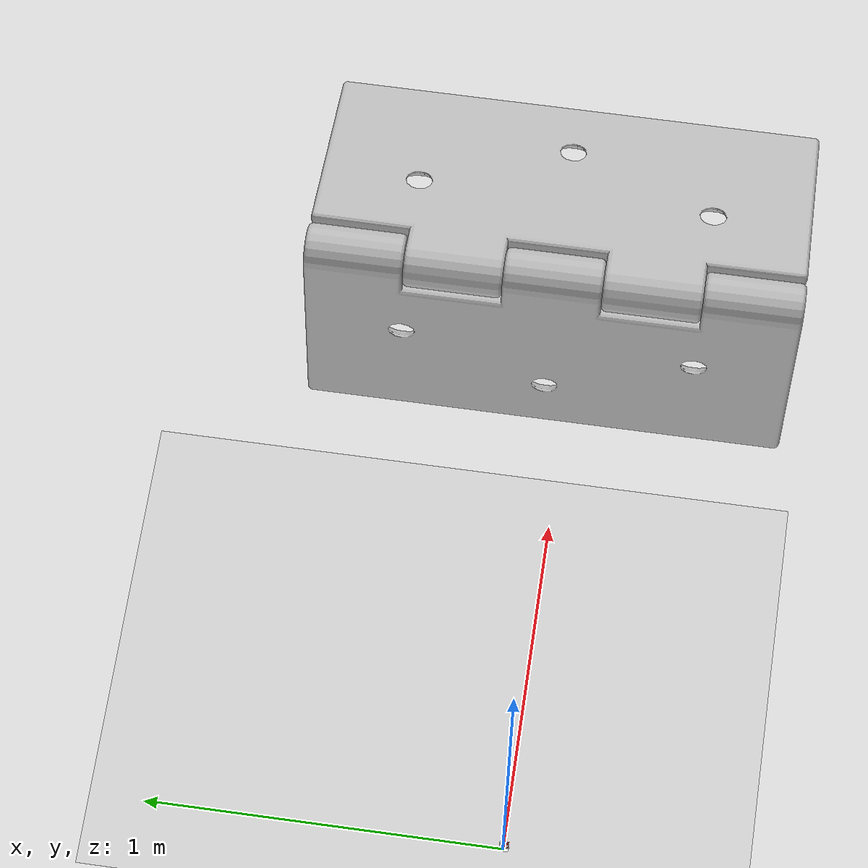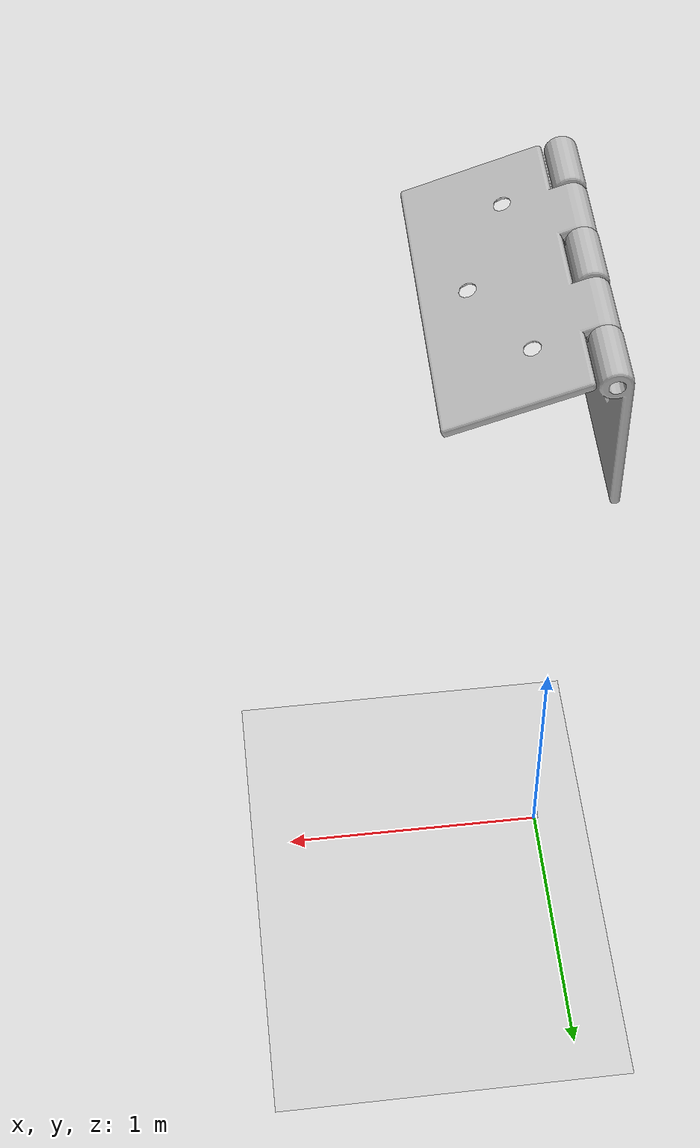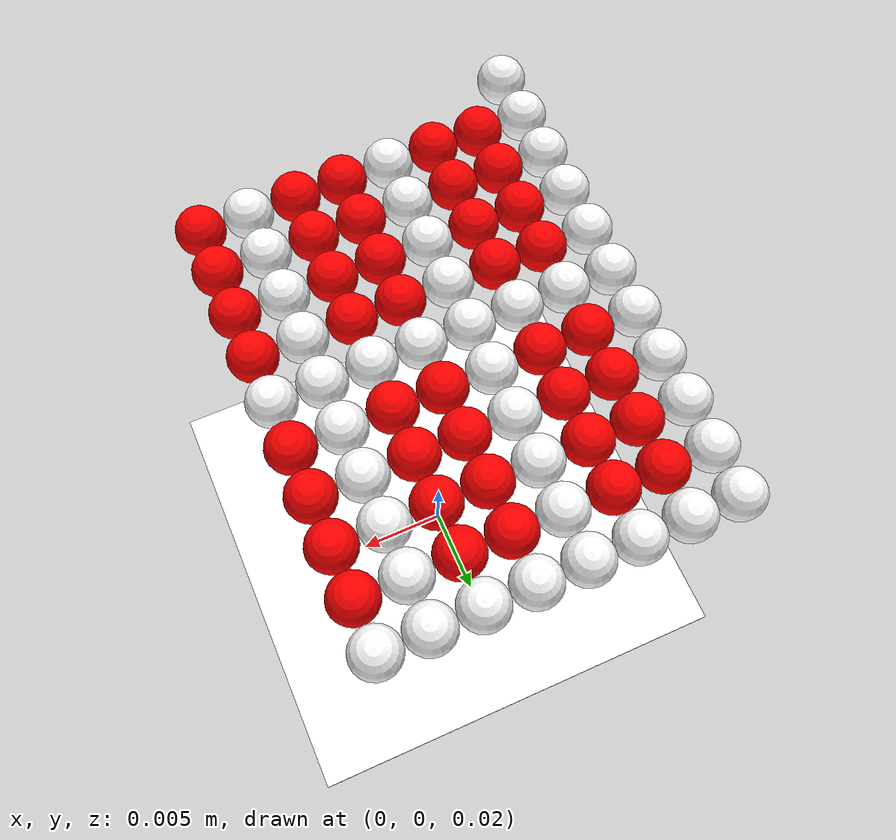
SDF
<?xml version="1.0"?>
<gazebo version="1.3">
<world name="default">

<include>
  <uri>model://ground_plane</uri>
</include>

<include>
  <uri>model://sun</uri>
</include>

<include>
  <uri>model://spring_board</uri>
</include>

<physics type="ode">
  <gravity>0.0 0.0 0.0</gravity>
</physics>

<include>
  <uri>model://hinge</uri>
  <pose>0 0 2.8 0 0 -1.571</pose>
</include>

</world>
</gazebo>

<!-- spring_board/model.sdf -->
<sdf version='1.4'>
  <model name='spring_board'>
    <pose>0 0 0 0 -0 0</pose>
    <link name='plane'>
      <pose>0 0 0.02 0 -0 0</pose>
      <inertial>
        <mass>20</mass>
      </inertial>
      <collision name='collision'>
        <geometry>
          <box>
            <size>0.025 0.025 0.00025</size>
          </box>
        </geometry>
        <surface>
          <friction>
            <ode>
              <mu>0</mu>
              <mu2>0</mu2>
            </ode>
          </friction>
        </surface>
      </collision>
      <visual name='visual'>
        <geometry>
          <box>
            <size>0.025 0.025 0.00025</size>
          </box>
        </geometry>
        <material>
          <ambient>1 1 1 1</ambient>
          <diffuse>1 1 1 1</diffuse>
          <specular>0.1 0.1 0.1 1</specular>
          <emissive>0 0 0 0</emissive>
        </material>
      </visual>
      <velocity_decay>
        <linear>0</linear>
        <angular>0</angular>
      </velocity_decay>
    </link>
    <joint name='plane_joint' type='prismatic'>
      <parent>world</parent>
      <child>plane</child>
      <axis>
        <xyz>0 0 1</xyz>
        <limit>
          <lower>0</lower>
          <upper>0</upper>
        </limit>
      </axis>
    </joint>
    <link name='spring_1'>
      <pose>-0.01 0.01 0.04 0 -0 0</pose>
      <inertial>
        <mass>0.00235</mass>
      </inertial>
      <collision name='sphere_collision'>
        <geometry>
          <sphere>
            <radius>0.00125</radius>
          </sphere>
        </geometry>
        <surface>
          <friction>
            <ode>
              <mu>0</mu>
              <mu2>0</mu2>
            </ode>
          </friction>
        </surface>
      </collision>
      <visual name='visual'>
        <geometry>
          <sphere>
            <radius>0.00125</radius>
          </sphere>
        </geometry>
        <material>
          <ambient>1 1 1 1</ambient>
          <diffuse>1 1 1 1</diffuse>
          <specular>0.1 0.1 0.1 1</specular>
          <emissive>0 0 0 0</emissive>
        </material>
      </visual>
      <velocity_decay>
        <linear>0</linear>
        <angular>0</angular>
      </velocity_decay>
    </link>
    <joint name='spring_joint_1' type='prismatic'>
      <parent>plane</parent>
      <child>spring_1</child>
      <axis>
        <xyz>0 0 1</xyz>
        <limit>
          <lower>-1e+16</lower>
          <upper>1e+16</upper>
        </limit>
      </axis>
    </joint>
    <link name='spring_2'>
      <pose>-0.0075 0.01 0.04 0 -0 0</pose>
      <inertial>
        <mass>0.00235</mass>
      </inertial>
      <collision name='sphere_collision'>
        <geometry>
          <sphere>
            <radius>0.00125</radius>
          </sphere>
        </geometry>
        <surface>
          <friction>
            <ode>
              <mu>0</mu>
              <mu2>0</mu2>
            </ode>
          </friction>
        </surface>
      </collision>
      <visual name='visual'>
        <geometry>
          <sphere>
            <radius>0.00125</radius>
          </sphere>
        </geometry>
        <material>
          <ambient>1 1 1 1</ambient>
          <diffuse>1 1 1 1</diffuse>
          <specular>0.1 0.1 0.1 1</specular>
          <emissive>0 0 0 0</emissive>
        </material>
      </visual>
      <velocity_decay>
        <linear>0</linear>
        <angular>0</angular>
      </velocity_decay>
    </link>
    <joint name='spring_joint_2' type='prismatic'>
      <parent>plane</parent>
      <child>spring_2</child>
      <axis>
        <xyz>0 0 1</xyz>
        <limit>
          <lower>-1e+16</lower>
          <upper>1e+16</upper>
        </limit>
      </axis>
    </joint>
    <link name='spring_3'>
      <pose>-0.005 0.01 0.04 0 -0 0</pose>
      <inertial>
        <mass>0.00235</mass>
      </inertial>
      <collision name='sphere_collision'>
        <geometry>
          <sphere>
            <radius>0.00125</radius>
          </sphere>
        </geometry>
        <surface>
          <friction>
            <ode>
              <mu>0</mu>
              <mu2>0</mu2>
            </ode>
          </friction>
        </surface>
      </collision>
      <visual name='visual'>
        <geometry>
          <sphere>
            <radius>0.00125</radius>
          </sphere>
        </geometry>
        <material>
          <ambient>1 1 1 1</ambient>
          <diffuse>1 1 1 1</diffuse>
          <specular>0.1 0.1 0.1 1</specular>
          <emissive>0 0 0 0</emissive>
        </material>
      </visual>
      <velocity_decay>
        <linear>0</linear>
        <angular>0</angular>
      </velocity_decay>
    </link>
    <joint name='spring_joint_3' type='prismatic'>
      <parent>plane</parent>
      <child>spring_3</child>
      <axis>
        <xyz>0 0 1</xyz>
        <limit>
          <lower>-1e+16</lower>
          <upper>1e+16</upper>
        </limit>
      </axis>
    </joint>
    <link name='spring_4'>
      <pose>-0.0025 0.01 0.04 0 -0 0</pose>
      <inertial>
        <mass>0.00235</mass>
      </inertial>
      <collision name='sphere_collision'>
        <geometry>
          <sphere>
            <radius>0.00125</radius>
          </sphere>
        </geometry>
        <surface>
          <friction>
            <ode>
              <mu>0</mu>
              <mu2>0</mu2>
            </ode>
          </friction>
        </surface>
      </collision>
      <visual name='visual'>
        <geometry>
          <sphere>
            <radius>0.00125</radius>
          </sphere>
        </geometry>
        <material>
          <ambient>1 1 1 1</ambient>
          <diffuse>1 1 1 1</diffuse>
          <specular>0.1 0.1 0.1 1</specular>
          <emissive>0 0 0 0</emissive>
        </material>
      </visual>
      <velocity_decay>
        <linear>0</linear>
        <angular>0</angular>
      </velocity_decay>
    </link>
    <joint name='spring_joint_4' type='prismatic'>
      <parent>plane</parent>
      <child>spring_4</child>
      <axis>
        <xyz>0 0 1</xyz>
        <limit>
          <lower>-1e+16</lower>
          <upper>1e+16</upper>
        </limit>
      </axis>
    </joint>
    <link name='spring_5'>
      <pose>8.67362e-19 0.01 0.04 0 -0 0</pose>
      <inertial>
        <mass>0.00235</mass>
      </inertial>
      <collision name='sphere_collision'>
        <geometry>
          <sphere>
            <radius>0.00125</radius>
          </sphere>
        </geometry>
        <surface>
          <friction>
            <ode>
              <mu>0</mu>
              <mu2>0</mu2>
            </ode>
          </friction>
        </surface>
      </collision>
      <visual name='visual'>
        <geometry>
          <sphere>
            <radius>0.00125</radius>
          </sphere>
        </geometry>
        <material>
          <ambient>1 1 1 1</ambient>
          <diffuse>1 1 1 1</diffuse>
          <specular>0.1 0.1 0.1 1</specular>
          <emissive>0 0 0 0</emissive>
        </material>
      </visual>
      <velocity_decay>
        <linear>0</linear>
        <angular>0</angular>
      </velocity_decay>
    </link>
    <joint name='spring_joint_5' type='prismatic'>
      <parent>plane</parent>
      <child>spring_5</child>
      <axis>
        <xyz>0 0 1</xyz>
        <limit>
          <lower>-1e+16</lower>
          <upper>1e+16</upper>
        </limit>
      </axis>
    </joint>
    <link name='spring_6'>
      <pose>0.0025 0.01 0.04 0 -0 0</pose>
      <inertial>
        <mass>0.00235</mass>
      </inertial>
      <collision name='sphere_collision'>
        <geometry>
          <sphere>
            <radius>0.00125</radius>
          </sphere>
        </geometry>
        <surface>
          <friction>
            <ode>
              <mu>0</mu>
              <mu2>0</mu2>
            </ode>
          </friction>
        </surface>
      </collision>
      <visual name='visual'>
        <geometry>
          <sphere>
            <radius>0.00125</radius>
          </sphere>
        </geometry>
        <material>
          <ambient>1 1 1 1</ambient>
          <diffuse>1 1 1 1</diffuse>
          <specular>0.1 0.1 0.1 1</specular>
          <emissive>0 0 0 0</emissive>
        </material>
      </visual>
      <velocity_decay>
        <linear>0</linear>
        <angular>0</angular>
      </velocity_decay>
    </link>
    <joint name='spring_joint_6' type='prismatic'>
      <parent>plane</parent>
      <child>spring_6</child>
      <axis>
        <xyz>0 0 1</xyz>
        <limit>
          <lower>-1e+16</lower>
          <upper>1e+16</upper>
        </limit>
      </axis>
    </joint>
    <link name='spring_7'>
      <pose>0.005 0.01 0.04 0 -0 0</pose>
      <inertial>
        <mass>0.00235</mass>
      </inertial>
      <collision name='sphere_collision'>
        <geometry>
          <sphere>
            <radius>0.00125</radius>
          </sphere>
        </geometry>
        <surface>
          <friction>
            <ode>
              <mu>0</mu>
              <mu2>0</mu2>
            </ode>
          </friction>
        </surface>
      </collision>
      <visual name='visual'>
        <geometry>
          <sphere>
            <radius>0.00125</radius>
          </sphere>
        </geometry>
        <material>
          <ambient>1 1 1 1</ambient>
          <diffuse>1 1 1 1</diffuse>
          <specular>0.1 0.1 0.1 1</specular>
          <emissive>0 0 0 0</emissive>
        </material>
      </visual>
      <velocity_decay>
        <linear>0</linear>
        <angular>0</angular>
      </velocity_decay>
    </link>
    <joint name='spring_joint_7' type='prismatic'>
      <parent>plane</parent>
      <child>spring_7</child>
      <axis>
        <xyz>0 0 1</xyz>
        <limit>
          <lower>-1e+16</lower>
          <upper>1e+16</upper>
        </limit>
      </axis>
    </joint>
    <link name='spring_8'>
      <pose>0.0075 0.01 0.04 0 -0 0</pose>
      <inertial>
        <mass>0.00235</mass>
      </inertial>
      <collision name='sphere_collision'>
        <geometry>
          <sphere>
            <radius>0.00125</radius>
          </sphere>
        </geometry>
        <surface>
          <friction>
            <ode>
              <mu>0</mu>
              <mu2>0</mu2>
            </ode>
          </friction>
        </surface>
      </collision>
      <visual name='visual'>
        <geometry>
          <sphere>
            <radius>0.00125</radius>
          </sphere>
        </geometry>
        <material>
          <ambient>1 1 1 1</ambient>
          <diffuse>1 1 1 1</diffuse>
          <specular>0.1 0.1 0.1 1</specular>
          <emissive>0 0 0 0</emissive>
        </material>
      </visual>
      <velocity_decay>
        <linear>0</linear>
        <angular>0</angular>
      </velocity_decay>
    </link>
    <joint name='spring_joint_8' type='prismatic'>
      <parent>plane</parent>
      <child>spring_8</child>
      <axis>
        <xyz>0 0 1</xyz>
        <limit>
          <lower>-1e+16</lower>
          <upper>1e+16</upper>
        </limit>
      </axis>
    </joint>
    <link name='spring_9'>
      <pose>-0.01 0.0075 0.04 0 -0 0</pose>
      <inertial>
        <mass>0.00235</mass>
      </inertial>
      <collision name='sphere_collision'>
        <geometry>
          <sphere>
            <radius>0.00125</radius>
          </sphere>
        </geometry>
        <surface>
          <friction>
            <ode>
              <mu>0</mu>
              <mu2>0</mu2>
            </ode>
          </friction>
        </surface>
      </collision>
      <visual name='visual'>
        <geometry>
          <sphere>
            <radius>0.00125</radius>
          </sphere>
        </geometry>
        <material>
          <ambient>1 1 1 1</ambient>
          <diffuse>1 1 1 1</diffuse>
          <specular>0.1 0.1 0.1 1</specular>
          <emissive>0 0 0 0</emissive>
        </material>
      </visual>
      <velocity_decay>
        <linear>0</linear>
        <angular>0</angular>
      </velocity_decay>
    </link>
    <joint name='spring_joint_9' type='prismatic'>
      <parent>plane</parent>
      <child>spring_9</child>
      <axis>
        <xyz>0 0 1</xyz>
        <limit>
          <lower>-1e+16</lower>
          <upper>1e+16</upper>
        </limit>
      </axis>
    </joint>
    <link name='spring_10'>
      <pose>-0.0075 0.0075 0.04 0 -0 0</pose>
      <inertial>
        <mass>0.00235</mass>
      </inertial>
      <collision name='sphere_collision'>
        <geometry>
          <sphere>
            <radius>0.00125</radius>
          </sphere>
        </geometry>
        <surface>
          <friction>
            <ode>
              <mu>0</mu>
              <mu2>0</mu2>
            </ode>
          </friction>
        </surface>
      </collision>
      <visual name='visual'>
        <geometry>
          <sphere>
            <radius>0.00125</radius>
          </sphere>
        </geometry>
        <material>
          <ambient>1 0 0 1</ambient>
          <diffuse>1 0 0 1</diffuse>
          <specular>0.1 0.1 0.1 1</specular>
          <emissive>0 0 0 0</emissive>
        </material>
      </visual>
      <velocity_decay>
        <linear>0</linear>
        <angular>0</angular>
      </velocity_decay>
    </link>
    <joint name='spring_joint_10' type='prismatic'>
      <parent>plane</parent>
      <child>spring_10</child>
      <axis>
        <xyz>0 0 1</xyz>
        <limit>
          <lower>-1e+16</lower>
          <upper>1e+16</upper>
        </limit>
      </axis>
    </joint>
    <link name='spring_11'>
      <pose>-0.005 0.0075 0.04 0 -0 0</pose>
      <inertial>
        <mass>0.00235</mass>
      </inertial>
      <collision name='sphere_collision'>
        <geometry>
          <sphere>
            <radius>0.00125</radius>
          </sphere>
        </geometry>
        <surface>
          <friction>
            <ode>
              <mu>0</mu>
              <mu2>0</mu2>
            </ode>
          </friction>
        </surface>
      </collision>
      <visual name='visual'>
        <geometry>
          <sphere>
            <radius>0.00125</radius>
          </sphere>
        </geometry>
        <material>
          <ambient>1 0 0 1</ambient>
          <diffuse>1 0 0 1</diffuse>
          <specular>0.1 0.1 0.1 1</specular>
          <emissive>0 0 0 0</emissive>
        </material>
      </visual>
      <velocity_decay>
        <linear>0</linear>
        <angular>0</angular>
      </velocity_decay>
    </link>
    <joint name='spring_joint_11' type='prismatic'>
      <parent>plane</parent>
      <child>spring_11</child>
      <axis>
        <xyz>0 0 1</xyz>
        <limit>
          <lower>-1e+16</lower>
          <upper>1e+16</upper>
        </limit>
      </axis>
    </joint>
    <link name='spring_12'>
      <pose>-0.0025 0.0075 0.04 0 -0 0</pose>
      <inertial>
        <mass>0.00235</mass>
      </inertial>
      <collision name='sphere_collision'>
        <geometry>
          <sphere>
            <radius>0.00125</radius>
          </sphere>
        </geometry>
        <surface>
          <friction>
            <ode>
              <mu>0</mu>
              <mu2>0</mu2>
            </ode>
          </friction>
        </surface>
      </collision>
      <visual name='visual'>
        <geometry>
          <sphere>
            <radius>0.00125</radius>
          </sphere>
        </geometry>
        <material>
          <ambient>1 1 1 1</ambient>
          <diffuse>1 1 1 1</diffuse>
          <specular>0.1 0.1 0.1 1</specular>
          <emissive>0 0 0 0</emissive>
        </material>
      </visual>
      <velocity_decay>
        <linear>0</linear>
        <angular>0</angular>
      </velocity_decay>
    </link>
    <joint name='spring_joint_12' type='prismatic'>
      <parent>plane</parent>
      <child>spring_12</child>
      <axis>
        <xyz>0 0 1</xyz>
        <limit>
          <lower>-1e+16</lower>
          <upper>1e+16</upper>
        </limit>
      </axis>
    </joint>
    <link name='spring_13'>
      <pose>8.67362e-19 0.0075 0.04 0 -0 0</pose>
      <inertial>
        <mass>0.00235</mass>
      </inertial>
      <collision name='sphere_collision'>
        <geometry>
          <sphere>
            <radius>0.00125</radius>
          </sphere>
        </geometry>
        <surface>
          <friction>
            <ode>
              <mu>0</mu>
              <mu2>0</mu2>
            </ode>
          </friction>
        </surface>
      </collision>
      <visual name='visual'>
        <geometry>
          <sphere>
            <radius>0.00125</radius>
          </sphere>
        </geometry>
        <material>
          <ambient>1 0 0 1</ambient>
          <diffuse>1 0 0 1</diffuse>
          <specular>0.1 0.1 0.1 1</specular>
          <emissive>0 0 0 0</emissive>
        </material>
      </visual>
      <velocity_decay>
        <linear>0</linear>
        <angular>0</angular>
      </velocity_decay>
    </link>
    <joint name='spring_joint_13' type='prismatic'>
      <parent>plane</parent>
      <child>spring_13</child>
      <axis>
        <xyz>0 0 1</xyz>
        <limit>
          <lower>-1e+16</lower>
          <upper>1e+16</upper>
        </limit>
      </axis>
    </joint>
    <link name='spring_14'>
      <pose>0.0025 0.0075 0.04 0 -0 0</pose>
      <inertial>
        <mass>0.00235</mass>
      </inertial>
      <collision name='sphere_collision'>
        <geometry>
          <sphere>
            <radius>0.00125</radius>
          </sphere>
        </geometry>
        <surface>
          <friction>
            <ode>
              <mu>0</mu>
              <mu2>0</mu2>
            </ode>
          </friction>
        </surface>
      </collision>
      <visual name='visual'>
        <geometry>
          <sphere>
            <radius>0.00125</radius>
          </sphere>
        </geometry>
        <material>
          <ambient>1 0 0 1</ambient>
          <diffuse>1 0 0 1</diffuse>
          <specular>0.1 0.1 0.1 1</specular>
          <emissive>0 0 0 0</emissive>
        </material>
      </visual>
      <velocity_decay>
        <linear>0</linear>
        <angular>0</angular>
      </velocity_decay>
    </link>
    <joint name='spring_joint_14' type='prismatic'>
      <parent>plane</parent>
      <child>spring_14</child>
      <axis>
        <xyz>0 0 1</xyz>
        <limit>
          <lower>-1e+16</lower>
          <upper>1e+16</upper>
        </limit>
      </axis>
    </joint>
    <link name='spring_15'>
      <pose>0.005 0.0075 0.04 0 -0 0</pose>
      <inertial>
        <mass>0.00235</mass>
      </inertial>
      <collision name='sphere_collision'>
        <geometry>
          <sphere>
            <radius>0.00125</radius>
          </sphere>
        </geometry>
        <surface>
          <friction>
            <ode>
              <mu>0</mu>
              <mu2>0</mu2>
            </ode>
          </friction>
        </surface>
      </collision>
      <visual name='visual'>
        <geometry>
          <sphere>
            <radius>0.00125</radius>
          </sphere>
        </geometry>
        <material>
          <ambient>1 1 1 1</ambient>
          <diffuse>1 1 1 1</diffuse>
          <specular>0.1 0.1 0.1 1</specular>
          <emissive>0 0 0 0</emissive>
        </material>
      </visual>
      <velocity_decay>
        <linear>0</linear>
        <angular>0</angular>
      </velocity_decay>
    </link>
    <joint name='spring_joint_15' type='prismatic'>
      <parent>plane</parent>
      <child>spring_15</child>
      <axis>
        <xyz>0 0 1</xyz>
        <limit>
          <lower>-1e+16</lower>
          <upper>1e+16</upper>
        </limit>
      </axis>
    </joint>
    <link name='spring_16'>
      <pose>0.0075 0.0075 0.04 0 -0 0</pose>
      <inertial>
        <mass>0.00235</mass>
      </inertial>
      <collision name='sphere_collision'>
        <geometry>
          <sphere>
            <radius>0.00125</radius>
          </sphere>
        </geometry>
        <surface>
          <friction>
            <ode>
              <mu>0</mu>
              <mu2>0</mu2>
            </ode>
          </friction>
        </surface>
      </collision>
      <visual name='visual'>
        <geometry>
          <sphere>
            <radius>0.00125</radius>
          </sphere>
        </geometry>
        <material>
          <ambient>1 0 0 1</ambient>
          <diffuse>1 0 0 1</diffuse>
          <specular>0.1 0.1 0.1 1</specular>
          <emissive>0 0 0 0</emissive>
        </material>
      </visual>
      <velocity_decay>
        <linear>0</linear>
        <angular>0</angular>
      </velocity_decay>
    </link>
    <joint name='spring_joint_16' type='prismatic'>
      <parent>plane</parent>
      <child>spring_16</child>
      <axis>
        <xyz>0 0 1</xyz>
        <limit>
          <lower>-1e+16</lower>
          <upper>1e+16</upper>
        </limit>
      </axis>
    </joint>
    <link name='spring_17'>
      <pose>-0.01 0.005 0.04 0 -0 0</pose>
      <inertial>
        <mass>0.00235</mass>
      </inertial>
      <collision name='sphere_collision'>
        <geometry>
          <sphere>
            <radius>0.00125</radius>
          </sphere>
        </geometry>
        <surface>
          <friction>
            <ode>
              <mu>0</mu>
              <mu2>0</mu2>
            </ode>
          </friction>
        </surface>
      </collision>
      <visual name='visual'>
        <geometry>
          <sphere>
            <radius>0.00125</radius>
          </sphere>
        </geometry>
        <material>
          <ambient>1 1 1 1</ambient>
          <diffuse>1 1 1 1</diffuse>
          <specular>0.1 0.1 0.1 1</specular>
          <emissive>0 0 0 0</emissive>
        </material>
      </visual>
      <velocity_decay>
        <linear>0</linear>
        <angular>0</angular>
      </velocity_decay>
    </link>
    <joint name='spring_joint_17' type='prismatic'>
      <parent>plane</parent>
      <child>spring_17</child>
      <axis>
        <xyz>0 0 1</xyz>
        <limit>
          <lower>-1e+16</lower>
          <upper>1e+16</upper>
        </limit>
      </axis>
    </joint>
    <link name='spring_18'>
      <pose>-0.0075 0.005 0.04 0 -0 0</pose>
      <inertial>
        <mass>0.00235</mass>
      </inertial>
      <collision name='sphere_collision'>
        <geometry>
          <sphere>
            <radius>0.00125</radius>
          </sphere>
        </geometry>
        <surface>
          <friction>
            <ode>
              <mu>0</mu>
              <mu2>0</mu2>
            </ode>
          </friction>
        </surface>
      </collision>
      <visual name='visual'>
        <geometry>
          <sphere>
            <radius>0.00125</radius>
          </sphere>
        </geometry>
        <material>
          <ambient>1 0 0 1</ambient>
          <diffuse>1 0 0 1</diffuse>
          <specular>0.1 0.1 0.1 1</specular>
          <emissive>0 0 0 0</emissive>
        </material>
      </visual>
      <velocity_decay>
        <linear>0</linear>
        <angular>0</angular>
      </velocity_decay>
    </link>
    <joint name='spring_joint_18' type='prismatic'>
      <parent>plane</parent>
      <child>spring_18</child>
      <axis>
        <xyz>0 0 1</xyz>
        <limit>
          <lower>-1e+16</lower>
          <upper>1e+16</upper>
        </limit>
      </axis>
    </joint>
    <link name='spring_19'>
      <pose>-0.005 0.005 0.04 0 -0 0</pose>
      <inertial>
        <mass>0.00235</mass>
      </inertial>
      <collision name='sphere_collision'>
        <geometry>
          <sphere>
            <radius>0.00125</radius>
          </sphere>
        </geometry>
        <surface>
          <friction>
            <ode>
              <mu>0</mu>
              <mu2>0</mu2>
            </ode>
          </friction>
        </surface>
      </collision>
      <visual name='visual'>
        <geometry>
          <sphere>
            <radius>0.00125</radius>
          </sphere>
        </geometry>
        <material>
          <ambient>1 0 0 1</ambient>
          <diffuse>1 0 0 1</diffuse>
          <specular>0.1 0.1 0.1 1</specular>
          <emissive>0 0 0 0</emissive>
        </material>
      </visual>
      <velocity_decay>
        <linear>0</linear>
        <angular>0</angular>
      </velocity_decay>
    </link>
    <joint name='spring_joint_19' type='prismatic'>
      <parent>plane</parent>
      <child>spring_19</child>
      <axis>
        <xyz>0 0 1</xyz>
        <limit>
          <lower>-1e+16</lower>
          <upper>1e+16</upper>
        </limit>
      </axis>
    </joint>
    <link name='spring_20'>
      <pose>-0.0025 0.005 0.04 0 -0 0</pose>
      <inertial>
        <mass>0.00235</mass>
      </inertial>
      <collision name='sphere_collision'>
        <geometry>
          <sphere>
            <radius>0.00125</radius>
          </sphere>
        </geometry>
        <surface>
          <friction>
            <ode>
              <mu>0</mu>
              <mu2>0</mu2>
            </ode>
          </friction>
        </surface>
      </collision>
      <visual name='visual'>
        <geometry>
          <sphere>
            <radius>0.00125</radius>
          </sphere>
        </geometry>
        <material>
          <ambient>1 1 1 1</ambient>
          <diffuse>1 1 1 1</diffuse>
          <specular>0.1 0.1 0.1 1</specular>
          <emissive>0 0 0 0</emissive>
        </material>
      </visual>
      <velocity_decay>
        <linear>0</linear>
        <angular>0</angular>
      </velocity_decay>
    </link>
    <joint name='spring_joint_20' type='prismatic'>
      <parent>plane</parent>
      <child>spring_20</child>
      <axis>
        <xyz>0 0 1</xyz>
        <limit>
          <lower>-1e+16</lower>
          <upper>1e+16</upper>
        </limit>
      </axis>
    </joint>
    <link name='spring_21'>
      <pose>8.67362e-19 0.005 0.04 0 -0 0</pose>
      <inertial>
        <mass>0.00235</mass>
      </inertial>
      <collision name='sphere_collision'>
        <geometry>
          <sphere>
            <radius>0.00125</radius>
          </sphere>
        </geometry>
        <surface>
          <friction>
            <ode>
              <mu>0</mu>
              <mu2>0</mu2>
            </ode>
          </friction>
        </surface>
      </collision>
      <visual name='visual'>
        <geometry>
          <sphere>
            <radius>0.00125</radius>
          </sphere>
        </geometry>
        <material>
          <ambient>1 0 0 1</ambient>
          <diffuse>1 0 0 1</diffuse>
          <specular>0.1 0.1 0.1 1</specular>
          <emissive>0 0 0 0</emissive>
        </material>
      </visual>
      <velocity_decay>
        <linear>0</linear>
        <angular>0</angular>
      </velocity_decay>
    </link>
    <joint name='spring_joint_21' type='prismatic'>
      <parent>plane</parent>
      <child>spring_21</child>
      <axis>
        <xyz>0 0 1</xyz>
        <limit>
          <lower>-1e+16</lower>
          <upper>1e+16</upper>
        </limit>
      </axis>
    </joint>
    <link name='spring_22'>
      <pose>0.0025 0.005 0.04 0 -0 0</pose>
      <inertial>
        <mass>0.00235</mass>
      </inertial>
      <collision name='sphere_collision'>
        <geometry>
          <sphere>
            <radius>0.00125</radius>
          </sphere>
        </geometry>
        <surface>
          <friction>
            <ode>
              <mu>0</mu>
              <mu2>0</mu2>
            </ode>
          </friction>
        </surface>
      </collision>
      <visual name='visual'>
        <geometry>
          <sphere>
            <radius>0.00125</radius>
          </sphere>
        </geometry>
        <material>
          <ambient>1 0 0 1</ambient>
          <diffuse>1 0 0 1</diffuse>
          <specular>0.1 0.1 0.1 1</specular>
          <emissive>0 0 0 0</emissive>
        </material>
      </visual>
      <velocity_decay>
        <linear>0</linear>
        <angular>0</angular>
      </velocity_decay>
    </link>
    <joint name='spring_joint_22' type='prismatic'>
      <parent>plane</parent>
      <child>spring_22</child>
      <axis>
        <xyz>0 0 1</xyz>
        <limit>
          <lower>-1e+16</lower>
          <upper>1e+16</upper>
        </limit>
      </axis>
    </joint>
    <link name='spring_23'>
      <pose>0.005 0.005 0.04 0 -0 0</pose>
      <inertial>
        <mass>0.00235</mass>
      </inertial>
      <collision name='sphere_collision'>
        <geometry>
          <sphere>
            <radius>0.00125</radius>
          </sphere>
        </geometry>
        <surface>
          <friction>
            <ode>
              <mu>0</mu>
              <mu2>0</mu2>
            </ode>
          </friction>
        </surface>
      </collision>
      <visual name='visual'>
        <geometry>
          <sphere>
            <radius>0.00125</radius>
          </sphere>
        </geometry>
        <material>
          <ambient>1 1 1 1</ambient>
          <diffuse>1 1 1 1</diffuse>
          <specular>0.1 0.1 0.1 1</specular>
          <emissive>0 0 0 0</emissive>
        </material>
      </visual>
      <velocity_decay>
        <linear>0</linear>
        <angular>0</angular>
      </velocity_decay>
    </link>
    <joint name='spring_joint_23' type='prismatic'>
      <parent>plane</parent>
      <child>spring_23</child>
      <axis>
        <xyz>0 0 1</xyz>
        <limit>
          <lower>-1e+16</lower>
          <upper>1e+16</upper>
        </limit>
      </axis>
    </joint>
    <link name='spring_24'>
      <pose>0.0075 0.005 0.04 0 -0 0</pose>
      <inertial>
        <mass>0.00235</mass>
      </inertial>
      <collision name='sphere_collision'>
        <geometry>
          <sphere>
            <radius>0.00125</radius>
          </sphere>
        </geometry>
        <surface>
          <friction>
            <ode>
              <mu>0</mu>
              <mu2>0</mu2>
            </ode>
          </friction>
        </surface>
      </collision>
      <visual name='visual'>
        <geometry>
          <sphere>
            <radius>0.00125</radius>
          </sphere>
        </geometry>
        <material>
          <ambient>1 0 0 1</ambient>
          <diffuse>1 0 0 1</diffuse>
          <specular>0.1 0.1 0.1 1</specular>
          <emissive>0 0 0 0</emissive>
        </material>
      </visual>
      <velocity_decay>
        <linear>0</linear>
        <angular>0</angular>
      </velocity_decay>
    </link>
    <joint name='spring_joint_24' type='prismatic'>
      <parent>plane</parent>
      <child>spring_24</child>
      <axis>
        <xyz>0 0 1</xyz>
        <limit>
          <lower>-1e+16</lower>
          <upper>1e+16</upper>
        </limit>
      </axis>
    </joint>
    <link name='spring_25'>
      <pose>-0.01 0.0025 0.04 0 -0 0</pose>
      <inertial>
        <mass>0.00235</mass>
      </inertial>
      <collision name='sphere_collision'>
        <geometry>
          <sphere>
            <radius>0.00125</radius>
          </sphere>
        </geometry>
        <surface>
          <friction>
            <ode>
              <mu>0</mu>
              <mu2>0</mu2>
            </ode>
          </friction>
        </surface>
      </collision>
      <visual name='visual'>
        <geometry>
          <sphere>
            <radius>0.00125</radius>
          </sphere>
        </geometry>
        <material>
          <ambient>1 1 1 1</ambient>
          <diffuse>1 1 1 1</diffuse>
          <specular>0.1 0.1 0.1 1</specular>
          <emissive>0 0 0 0</emissive>
        </material>
      </visual>
      <velocity_decay>
        <linear>0</linear>
        <angular>0</angular>
      </velocity_decay>
    </link>
    <joint name='spring_joint_25' type='prismatic'>
      <parent>plane</parent>
      <child>spring_25</child>
      <axis>
        <xyz>0 0 1</xyz>
        <limit>
          <lower>-1e+16</lower>
          <upper>1e+16</upper>
        </limit>
      </axis>
    </joint>
    <link name='spring_26'>
      <pose>-0.0075 0.0025 0.04 0 -0 0</pose>
      <inertial>
        <mass>0.00235</mass>
      </inertial>
      <collision name='sphere_collision'>
        <geometry>
          <sphere>
            <radius>0.00125</radius>
          </sphere>
        </geometry>
        <surface>
          <friction>
            <ode>
              <mu>0</mu>
              <mu2>0</mu2>
            </ode>
          </friction>
        </surface>
      </collision>
      <visual name='visual'>
        <geometry>
          <sphere>
            <radius>0.00125</radius>
          </sphere>
        </geometry>
        <material>
          <ambient>1 0 0 1</ambient>
          <diffuse>1 0 0 1</diffuse>
          <specular>0.1 0.1 0.1 1</specular>
          <emissive>0 0 0 0</emissive>
        </material>
      </visual>
      <velocity_decay>
        <linear>0</linear>
        <angular>0</angular>
      </velocity_decay>
    </link>
    <joint name='spring_joint_26' type='prismatic'>
      <parent>plane</parent>
      <child>spring_26</child>
      <axis>
        <xyz>0 0 1</xyz>
        <limit>
          <lower>-1e+16</lower>
          <upper>1e+16</upper>
        </limit>
      </axis>
    </joint>
    <link name='spring_27'>
      <pose>-0.005 0.0025 0.04 0 -0 0</pose>
      <inertial>
        <mass>0.00235</mass>
      </inertial>
      <collision name='sphere_collision'>
        <geometry>
          <sphere>
            <radius>0.00125</radius>
          </sphere>
        </geometry>
        <surface>
          <friction>
            <ode>
              <mu>0</mu>
              <mu2>0</mu2>
            </ode>
          </friction>
        </surface>
      </collision>
      <visual name='visual'>
        <geometry>
          <sphere>
            <radius>0.00125</radius>
          </sphere>
        </geometry>
        <material>
          <ambient>1 0 0 1</ambient>
          <diffuse>1 0 0 1</diffuse>
          <specular>0.1 0.1 0.1 1</specular>
          <emissive>0 0 0 0</emissive>
        </material>
      </visual>
      <velocity_decay>
        <linear>0</linear>
        <angular>0</angular>
      </velocity_decay>
    </link>
    <joint name='spring_joint_27' type='prismatic'>
      <parent>plane</parent>
      <child>spring_27</child>
      <axis>
        <xyz>0 0 1</xyz>
        <limit>
          <lower>-1e+16</lower>
          <upper>1e+16</upper>
        </limit>
      </axis>
    </joint>
    <link name='spring_28'>
      <pose>-0.0025 0.0025 0.04 0 -0 0</pose>
      <inertial>
        <mass>0.00235</mass>
      </inertial>
      <collision name='sphere_collision'>
        <geometry>
          <sphere>
            <radius>0.00125</radius>
          </sphere>
        </geometry>
        <surface>
          <friction>
            <ode>
              <mu>0</mu>
              <mu2>0</mu2>
            </ode>
          </friction>
        </surface>
      </collision>
      <visual name='visual'>
        <geometry>
          <sphere>
            <radius>0.00125</radius>
          </sphere>
        </geometry>
        <material>
          <ambient>1 1 1 1</ambient>
          <diffuse>1 1 1 1</diffuse>
          <specular>0.1 0.1 0.1 1</specular>
          <emissive>0 0 0 0</emissive>
        </material>
      </visual>
      <velocity_decay>
        <linear>0</linear>
        <angular>0</angular>
      </velocity_decay>
    </link>
    <joint name='spring_joint_28' type='prismatic'>
      <parent>plane</parent>
      <child>spring_28</child>
      <axis>
        <xyz>0 0 1</xyz>
        <limit>
          <lower>-1e+16</lower>
          <upper>1e+16</upper>
        </limit>
      </axis>
    </joint>
    <link name='spring_29'>
      <pose>8.67362e-19 0.0025 0.04 0 -0 0</pose>
      <inertial>
        <mass>0.00235</mass>
      </inertial>
      <collision name='sphere_collision'>
        <geometry>
          <sphere>
            <radius>0.00125</radius>
          </sphere>
        </geometry>
        <surface>
          <friction>
            <ode>
              <mu>0</mu>
              <mu2>0</mu2>
            </ode>
          </friction>
        </surface>
      </collision>
      <visual name='visual'>
        <geometry>
          <sphere>
            <radius>0.00125</radius>
          </sphere>
        </geometry>
        <material>
          <ambient>1 0 0 1</ambient>
          <diffuse>1 0 0 1</diffuse>
          <specular>0.1 0.1 0.1 1</specular>
          <emissive>0 0 0 0</emissive>
        </material>
      </visual>
      <velocity_decay>
        <linear>0</linear>
        <angular>0</angular>
      </velocity_decay>
    </link>
    <joint name='spring_joint_29' type='prismatic'>
      <parent>plane</parent>
      <child>spring_29</child>
      <axis>
        <xyz>0 0 1</xyz>
        <limit>
          <lower>-1e+16</lower>
          <upper>1e+16</upper>
        </limit>
      </axis>
    </joint>
    <link name='spring_30'>
      <pose>0.0025 0.0025 0.04 0 -0 0</pose>
      <inertial>
        <mass>0.00235</mass>
      </inertial>
      <collision name='sphere_collision'>
        <geometry>
          <sphere>
            <radius>0.00125</radius>
          </sphere>
        </geometry>
        <surface>
          <friction>
            <ode>
              <mu>0</mu>
              <mu2>0</mu2>
            </ode>
          </friction>
        </surface>
      </collision>
      <visual name='visual'>
        <geometry>
          <sphere>
            <radius>0.00125</radius>
          </sphere>
        </geometry>
        <material>
          <ambient>1 0 0 1</ambient>
          <diffuse>1 0 0 1</diffuse>
          <specular>0.1 0.1 0.1 1</specular>
          <emissive>0 0 0 0</emissive>
        </material>
      </visual>
      <velocity_decay>
        <linear>0</linear>
        <angular>0</angular>
      </velocity_decay>
    </link>
    <joint name='spring_joint_30' type='prismatic'>
      <parent>plane</parent>
      <child>spring_30</child>
      <axis>
        <xyz>0 0 1</xyz>
        <limit>
          <lower>-1e+16</lower>
          <upper>1e+16</upper>
        </limit>
      </axis>
    </joint>
    <link name='spring_31'>
      <pose>0.005 0.0025 0.04 0 -0 0</pose>
      <inertial>
        <mass>0.00235</mass>
      </inertial>
      <collision name='sphere_collision'>
        <geometry>
          <sphere>
            <radius>0.00125</radius>
          </sphere>
        </geometry>
        <surface>
          <friction>
            <ode>
              <mu>0</mu>
              <mu2>0</mu2>
            </ode>
          </friction>
        </surface>
      </collision>
      <visual name='visual'>
        <geometry>
          <sphere>
            <radius>0.00125</radius>
          </sphere>
        </geometry>
        <material>
          <ambient>1 1 1 1</ambient>
          <diffuse>1 1 1 1</diffuse>
          <specular>0.1 0.1 0.1 1</specular>
          <emissive>0 0 0 0</emissive>
        </material>
      </visual>
      <velocity_decay>
        <linear>0</linear>
        <angular>0</angular>
      </velocity_decay>
    </link>
    <joint name='spring_joint_31' type='prismatic'>
      <parent>plane</parent>
      <child>spring_31</child>
      <axis>
        <xyz>0 0 1</xyz>
        <limit>
          <lower>-1e+16</lower>
          <upper>1e+16</upper>
        </limit>
      </axis>
    </joint>
    <link name='spring_32'>
      <pose>0.0075 0.0025 0.04 0 -0 0</pose>
      <inertial>
        <mass>0.00235</mass>
      </inertial>
      <collision name='sphere_collision'>
        <geometry>
          <sphere>
            <radius>0.00125</radius>
          </sphere>
        </geometry>
        <surface>
          <friction>
            <ode>
              <mu>0</mu>
              <mu2>0</mu2>
            </ode>
          </friction>
        </surface>
      </collision>
      <visual name='visual'>
        <geometry>
          <sphere>
            <radius>0.00125</radius>
          </sphere>
        </geometry>
        <material>
          <ambient>1 0 0 1</ambient>
          <diffuse>1 0 0 1</diffuse>
          <specular>0.1 0.1 0.1 1</specular>
          <emissive>0 0 0 0</emissive>
        </material>
      </visual>
      <velocity_decay>
        <linear>0</linear>
        <angular>0</angular>
      </velocity_decay>
    </link>
    <joint name='spring_joint_32' type='prismatic'>
      <parent>plane</parent>
      <child>spring_32</child>
      <axis>
        <xyz>0 0 1</xyz>
        <limit>
          <lower>-1e+16</lower>
          <upper>1e+16</upper>
        </limit>
      </axis>
    </joint>
    <link name='spring_33'>
      <pose>-0.01 -8.67362e-19 0.04 0 -0 0</pose>
      <inertial>
        <mass>0.00235</mass>
      </inertial>
      <collision name='sphere_collision'>
        <geometry>
          <sphere>
            <radius>0.00125</radius>
          </sphere>
        </geometry>
        <surface>
          <friction>
            <ode>
              <mu>0</mu>
              <mu2>0</mu2>
            </ode>
          </friction>
        </surface>
      </collision>
      <visual name='visual'>
        <geometry>
          <sphere>
            <radius>0.00125</radius>
          </sphere>
        </geometry>
        <material>
          <ambient>1 1 1 1</ambient>
          <diffuse>1 1 1 1</diffuse>
          <specular>0.1 0.1 0.1 1</specular>
          <emissive>0 0 0 0</emissive>
        </material>
      </visual>
      <velocity_decay>
        <linear>0</linear>
        <angular>0</angular>
      </velocity_decay>
    </link>
    <joint name='spring_joint_33' type='prismatic'>
      <parent>plane</parent>
      <child>spring_33</child>
      <axis>
        <xyz>0 0 1</xyz>
        <limit>
          <lower>-1e+16</lower>
          <upper>1e+16</upper>
        </limit>
      </axis>
    </joint>
    <link name='spring_34'>
      <pose>-0.0075 -8.67362e-19 0.04 0 -0 0</pose>
      <inertial>
        <mass>0.00235</mass>
      </inertial>
      <collision name='sphere_collision'>
        <geometry>
          <sphere>
            <radius>0.00125</radius>
          </sphere>
        </geometry>
        <surface>
          <friction>
            <ode>
              <mu>0</mu>
              <mu2>0</mu2>
            </ode>
          </friction>
        </surface>
      </collision>
      <visual name='visual'>
        <geometry>
          <sphere>
            <radius>0.00125</radius>
          </sphere>
        </geometry>
        <material>
          <ambient>1 0 0 1</ambient>
          <diffuse>1 0 0 1</diffuse>
          <specular>0.1 0.1 0.1 1</specular>
          <emissive>0 0 0 0</emissive>
        </material>
      </visual>
      <velocity_decay>
        <linear>0</linear>
        <angular>0</angular>
      </velocity_decay>
    </link>
    <joint name='spring_joint_34' type='prismatic'>
      <parent>plane</parent>
      <child>spring_34</child>
      <axis>
        <xyz>0 0 1</xyz>
        <limit>
          <lower>-1e+16</lower>
          <upper>1e+16</upper>
        </limit>
      </axis>
    </joint>
    <link name='spring_35'>
      <pose>-0.005 -8.67362e-19 0.04 0 -0 0</pose>
      <inertial>
        <mass>0.00235</mass>
      </inertial>
      <collision name='sphere_collision'>
        <geometry>
          <sphere>
            <radius>0.00125</radius>
          </sphere>
        </geometry>
        <surface>
          <friction>
            <ode>
              <mu>0</mu>
              <mu2>0</mu2>
            </ode>
          </friction>
        </surface>
      </collision>
      <visual name='visual'>
        <geometry>
          <sphere>
            <radius>0.00125</radius>
          </sphere>
        </geometry>
        <material>
          <ambient>1 0 0 1</ambient>
          <diffuse>1 0 0 1</diffuse>
          <specular>0.1 0.1 0.1 1</specular>
          <emissive>0 0 0 0</emissive>
        </material>
      </visual>
      <velocity_decay>
        <linear>0</linear>
        <angular>0</angular>
      </velocity_decay>
    </link>
    <joint name='spring_joint_35' type='prismatic'>
      <parent>plane</parent>
      <child>spring_35</child>
      <axis>
        <xyz>0 0 1</xyz>
        <limit>
          <lower>-1e+16</lower>
          <upper>1e+16</upper>
        </limit>
      </axis>
    </joint>
    <link name='spring_36'>
      <pose>-0.0025 -8.67362e-19 0.04 0 -0 0</pose>
      <inertial>
        <mass>0.00235</mass>
      </inertial>
      <collision name='sphere_collision'>
        <geometry>
          <sphere>
            <radius>0.00125</radius>
          </sphere>
        </geometry>
        <surface>
          <friction>
            <ode>
              <mu>0</mu>
              <mu2>0</mu2>
            </ode>
          </friction>
        </surface>
      </collision>
      <visual name='visual'>
        <geometry>
          <sphere>
            <radius>0.00125</radius>
          </sphere>
        </geometry>
        <material>
          <ambient>1 1 1 1</ambient>
          <diffuse>1 1 1 1</diffuse>
          <specular>0.1 0.1 0.1 1</specular>
          <emissive>0 0 0 0</emissive>
        </material>
      </visual>
      <velocity_decay>
        <linear>0</linear>
        <angular>0</angular>
      </velocity_decay>
    </link>
    <joint name='spring_joint_36' type='prismatic'>
      <parent>plane</parent>
      <child>spring_36</child>
      <axis>
        <xyz>0 0 1</xyz>
        <limit>
          <lower>-1e+16</lower>
          <upper>1e+16</upper>
        </limit>
      </axis>
    </joint>
    <link name='spring_37'>
      <pose>8.67362e-19 -8.67362e-19 0.04 0 -0 0</pose>
      <inertial>
        <mass>0.00235</mass>
      </inertial>
      <collision name='sphere_collision'>
        <geometry>
          <sphere>
            <radius>0.00125</radius>
          </sphere>
        </geometry>
        <surface>
          <friction>
            <ode>
              <mu>0</mu>
              <mu2>0</mu2>
            </ode>
          </friction>
        </surface>
      </collision>
      <visual name='visual'>
        <geometry>
          <sphere>
            <radius>0.00125</radius>
          </sphere>
        </geometry>
        <material>
          <ambient>1 0 0 1</ambient>
          <diffuse>1 0 0 1</diffuse>
          <specular>0.1 0.1 0.1 1</specular>
          <emissive>0 0 0 0</emissive>
        </material>
      </visual>
      <velocity_decay>
        <linear>0</linear>
        <angular>0</angular>
      </velocity_decay>
    </link>
    <joint name='spring_joint_37' type='prismatic'>
      <parent>plane</parent>
      <child>spring_37</child>
      <axis>
        <xyz>0 0 1</xyz>
        <limit>
          <lower>-1e+16</lower>
          <upper>1e+16</upper>
        </limit>
      </axis>
    </joint>
    <link name='spring_38'>
      <pose>0.0025 -8.67362e-19 0.04 0 -0 0</pose>
      <inertial>
        <mass>0.00235</mass>
      </inertial>
      <collision name='sphere_collision'>
        <geometry>
          <sphere>
            <radius>0.00125</radius>
          </sphere>
        </geometry>
        <surface>
          <friction>
            <ode>
              <mu>0</mu>
              <mu2>0</mu2>
            </ode>
          </friction>
        </surface>
      </collision>
      <visual name='visual'>
        <geometry>
          <sphere>
            <radius>0.00125</radius>
          </sphere>
        </geometry>
        <material>
          <ambient>1 0 0 1</ambient>
          <diffuse>1 0 0 1</diffuse>
          <specular>0.1 0.1 0.1 1</specular>
          <emissive>0 0 0 0</emissive>
        </material>
      </visual>
      <velocity_decay>
        <linear>0</linear>
        <angular>0</angular>
      </velocity_decay>
    </link>
    <joint name='spring_joint_38' type='prismatic'>
      <parent>plane</parent>
      <child>spring_38</child>
      <axis>
        <xyz>0 0 1</xyz>
        <limit>
          <lower>-1e+16</lower>
          <upper>1e+16</upper>
        </limit>
      </axis>
    </joint>
    <link name='spring_39'>
      <pose>0.005 -8.67362e-19 0.04 0 -0 0</pose>
      <inertial>
        <mass>0.00235</mass>
      </inertial>
      <collision name='sphere_collision'>
        <geometry>
          <sphere>
            <radius>0.00125</radius>
          </sphere>
        </geometry>
        <surface>
          <friction>
            <ode>
              <mu>0</mu>
              <mu2>0</mu2>
            </ode>
          </friction>
        </surface>
      </collision>
      <visual name='visual'>
        <geometry>
          <sphere>
            <radius>0.00125</radius>
          </sphere>
        </geometry>
        <material>
          <ambient>1 1 1 1</ambient>
          <diffuse>1 1 1 1</diffuse>
          <specular>0.1 0.1 0.1 1</specular>
          <emissive>0 0 0 0</emissive>
        </material>
      </visual>
      <velocity_decay>
        <linear>0</linear>
        <angular>0</angular>
      </velocity_decay>
    </link>
    <joint name='spring_joint_39' type='prismatic'>
      <parent>plane</parent>
      <child>spring_39</child>
      <axis>
        <xyz>0 0 1</xyz>
        <limit>
          <lower>-1e+16</lower>
          <upper>1e+16</upper>
        </limit>
      </axis>
    </joint>
    <link name='spring_40'>
      <pose>0.0075 -8.67362e-19 0.04 0 -0 0</pose>
      <inertial>
        <mass>0.00235</mass>
      </inertial>
      <collision name='sphere_collision'>
        <geometry>
          <sphere>
            <radius>0.00125</radius>
          </sphere>
        </geometry>
        <surface>
          <friction>
            <ode>
              <mu>0</mu>
              <mu2>0</mu2>
            </ode>
          </friction>
        </surface>
      </collision>
      <visual name='visual'>
        <geometry>
          <sphere>
            <radius>0.00125</radius>
          </sphere>
        </geometry>
        <material>
          <ambient>1 0 0 1</ambient>
          <diffuse>1 0 0 1</diffuse>
          <specular>0.1 0.1 0.1 1</specular>
          <emissive>0 0 0 0</emissive>
        </material>
      </visual>
      <velocity_decay>
        <linear>0</linear>
        <angular>0</angular>
      </velocity_decay>
    </link>
    <joint name='spring_joint_40' type='prismatic'>
      <parent>plane</parent>
      <child>spring_40</child>
      <axis>
        <xyz>0 0 1</xyz>
        <limit>
          <lower>-1e+16</lower>
          <upper>1e+16</upper>
        </limit>
      </axis>
    </joint>
    <link name='spring_41'>
      <pose>-0.01 -0.0025 0.04 0 -0 0</pose>
      <inertial>
        <mass>0.00235</mass>
      </inertial>
      <collision name='sphere_collision'>
        <geometry>
          <sphere>
            <radius>0.00125</radius>
          </sphere>
        </geometry>
        <surface>
          <friction>
            <ode>
              <mu>0</mu>
              <mu2>0</mu2>
            </ode>
          </friction>
        </surface>
      </collision>
      <visual name='visual'>
        <geometry>
          <sphere>
            <radius>0.00125</radius>
          </sphere>
        </geometry>
        <material>
          <ambient>1 1 1 1</ambient>
          <diffuse>1 1 1 1</diffuse>
          <specular>0.1 0.1 0.1 1</specular>
          <emissive>0 0 0 0</emissive>
        </material>
      </visual>
      <velocity_decay>
        <linear>0</linear>
        <angular>0</angular>
      </velocity_decay>
    </link>
    <joint name='spring_joint_41' type='prismatic'>
      <parent>plane</parent>
      <child>spring_41</child>
      <axis>
        <xyz>0 0 1</xyz>
        <limit>
          <lower>-1e+16</lower>
          <upper>1e+16</upper>
        </limit>
      </axis>
    </joint>
    <link name='spring_42'>
      <pose>-0.0075 -0.0025 0.04 0 -0 0</pose>
      <inertial>
        <mass>0.00235</mass>
      </inertial>
      <collision name='sphere_collision'>
        <geometry>
          <sphere>
            <radius>0.00125</radius>
          </sphere>
        </geometry>
        <surface>
          <friction>
            <ode>
              <mu>0</mu>
              <mu2>0</mu2>
            </ode>
          </friction>
        </surface>
      </collision>
      <visual name='visual'>
        <geometry>
          <sphere>
            <radius>0.00125</radius>
          </sphere>
        </geometry>
        <material>
          <ambient>1 1 1 1</ambient>
          <diffuse>1 1 1 1</diffuse>
          <specular>0.1 0.1 0.1 1</specular>
          <emissive>0 0 0 0</emissive>
        </material>
      </visual>
      <velocity_decay>
        <linear>0</linear>
        <angular>0</angular>
      </velocity_decay>
    </link>
    <joint name='spring_joint_42' type='prismatic'>
      <parent>plane</parent>
      <child>spring_42</child>
      <axis>
        <xyz>0 0 1</xyz>
        <limit>
          <lower>-1e+16</lower>
          <upper>1e+16</upper>
        </limit>
      </axis>
    </joint>
    <link name='spring_43'>
      <pose>-0.005 -0.0025 0.04 0 -0 0</pose>
      <inertial>
        <mass>0.00235</mass>
      </inertial>
      <collision name='sphere_collision'>
        <geometry>
          <sphere>
            <radius>0.00125</radius>
          </sphere>
        </geometry>
        <surface>
          <friction>
            <ode>
              <mu>0</mu>
              <mu2>0</mu2>
            </ode>
          </friction>
        </surface>
      </collision>
      <visual name='visual'>
        <geometry>
          <sphere>
            <radius>0.00125</radius>
          </sphere>
        </geometry>
        <material>
          <ambient>1 1 1 1</ambient>
          <diffuse>1 1 1 1</diffuse>
          <specular>0.1 0.1 0.1 1</specular>
          <emissive>0 0 0 0</emissive>
        </material>
      </visual>
      <velocity_decay>
        <linear>0</linear>
        <angular>0</angular>
      </velocity_decay>
    </link>
    <joint name='spring_joint_43' type='prismatic'>
      <parent>plane</parent>
      <child>spring_43</child>
      <axis>
        <xyz>0 0 1</xyz>
        <limit>
          <lower>-1e+16</lower>
          <upper>1e+16</upper>
        </limit>
      </axis>
    </joint>
    <link name='spring_44'>
      <pose>-0.0025 -0.0025 0.04 0 -0 0</pose>
      <inertial>
        <mass>0.00235</mass>
      </inertial>
      <collision name='sphere_collision'>
        <geometry>
          <sphere>
            <radius>0.00125</radius>
          </sphere>
        </geometry>
        <surface>
          <friction>
            <ode>
              <mu>0</mu>
              <mu2>0</mu2>
            </ode>
          </friction>
        </surface>
      </collision>
      <visual name='visual'>
        <geometry>
          <sphere>
            <radius>0.00125</radius>
          </sphere>
        </geometry>
        <material>
          <ambient>1 1 1 1</ambient>
          <diffuse>1 1 1 1</diffuse>
          <specular>0.1 0.1 0.1 1</specular>
          <emissive>0 0 0 0</emissive>
        </material>
      </visual>
      <velocity_decay>
        <linear>0</linear>
        <angular>0</angular>
      </velocity_decay>
    </link>
    <joint name='spring_joint_44' type='prismatic'>
      <parent>plane</parent>
      <child>spring_44</child>
      <axis>
        <xyz>0 0 1</xyz>
        <limit>
          <lower>-1e+16</lower>
          <upper>1e+16</upper>
        </limit>
      </axis>
    </joint>
    <link name='spring_45'>
      <pose>8.67362e-19 -0.0025 0.04 0 -0 0</pose>
      <inertial>
        <mass>0.00235</mass>
      </inertial>
      <collision name='sphere_collision'>
        <geometry>
          <sphere>
            <radius>0.00125</radius>
          </sphere>
        </geometry>
        <surface>
          <friction>
            <ode>
              <mu>0</mu>
              <mu2>0</mu2>
            </ode>
          </friction>
        </surface>
      </collision>
      <visual name='visual'>
        <geometry>
          <sphere>
            <radius>0.00125</radius>
          </sphere>
        </geometry>
        <material>
          <ambient>1 1 1 1</ambient>
          <diffuse>1 1 1 1</diffuse>
          <specular>0.1 0.1 0.1 1</specular>
          <emissive>0 0 0 0</emissive>
        </material>
      </visual>
      <velocity_decay>
        <linear>0</linear>
        <angular>0</angular>
      </velocity_decay>
    </link>
    <joint name='spring_joint_45' type='prismatic'>
      <parent>plane</parent>
      <child>spring_45</child>
      <axis>
        <xyz>0 0 1</xyz>
        <limit>
          <lower>-1e+16</lower>
          <upper>1e+16</upper>
        </limit>
      </axis>
    </joint>
    <link name='spring_46'>
      <pose>0.0025 -0.0025 0.04 0 -0 0</pose>
      <inertial>
        <mass>0.00235</mass>
      </inertial>
      <collision name='sphere_collision'>
        <geometry>
          <sphere>
            <radius>0.00125</radius>
          </sphere>
        </geometry>
        <surface>
          <friction>
            <ode>
              <mu>0</mu>
              <mu2>0</mu2>
            </ode>
          </friction>
        </surface>
      </collision>
      <visual name='visual'>
        <geometry>
          <sphere>
            <radius>0.00125</radius>
          </sphere>
        </geometry>
        <material>
          <ambient>1 1 1 1</ambient>
          <diffuse>1 1 1 1</diffuse>
          <specular>0.1 0.1 0.1 1</specular>
          <emissive>0 0 0 0</emissive>
        </material>
      </visual>
      <velocity_decay>
        <linear>0</linear>
        <angular>0</angular>
      </velocity_decay>
    </link>
    <joint name='spring_joint_46' type='prismatic'>
      <parent>plane</parent>
      <child>spring_46</child>
      <axis>
        <xyz>0 0 1</xyz>
        <limit>
          <lower>-1e+16</lower>
          <upper>1e+16</upper>
        </limit>
      </axis>
    </joint>
    <link name='spring_47'>
      <pose>0.005 -0.0025 0.04 0 -0 0</pose>
      <inertial>
        <mass>0.00235</mass>
      </inertial>
      <collision name='sphere_collision'>
        <geometry>
          <sphere>
            <radius>0.00125</radius>
          </sphere>
        </geometry>
        <surface>
          <friction>
            <ode>
              <mu>0</mu>
              <mu2>0</mu2>
            </ode>
          </friction>
        </surface>
      </collision>
      <visual name='visual'>
        <geometry>
          <sphere>
            <radius>0.00125</radius>
          </sphere>
        </geometry>
        <material>
          <ambient>1 1 1 1</ambient>
          <diffuse>1 1 1 1</diffuse>
          <specular>0.1 0.1 0.1 1</specular>
          <emissive>0 0 0 0</emissive>
        </material>
      </visual>
      <velocity_decay>
        <linear>0</linear>
        <angular>0</angular>
      </velocity_decay>
    </link>
    <joint name='spring_joint_47' type='prismatic'>
      <parent>plane</parent>
      <child>spring_47</child>
      <axis>
        <xyz>0 0 1</xyz>
        <limit>
          <lower>-1e+16</lower>
          <upper>1e+16</upper>
        </limit>
      </axis>
    </joint>
    <link name='spring_48'>
      <pose>0.0075 -0.0025 0.04 0 -0 0</pose>
      <inertial>
        <mass>0.00235</mass>
      </inertial>
      <collision name='sphere_collision'>
        <geometry>
          <sphere>
            <radius>0.00125</radius>
          </sphere>
        </geometry>
        <surface>
          <friction>
            <ode>
              <mu>0</mu>
              <mu2>0</mu2>
            </ode>
          </friction>
        </surface>
      </collision>
      <visual name='visual'>
        <geometry>
          <sphere>
            <radius>0.00125</radius>
          </sphere>
        </geometry>
        <material>
          <ambient>1 1 1 1</ambient>
          <diffuse>1 1 1 1</diffuse>
          <specular>0.1 0.1 0.1 1</specular>
          <emissive>0 0 0 0</emissive>
        </material>
      </visual>
      <velocity_decay>
        <linear>0</linear>
        <angular>0</angular>
      </velocity_decay>
    </link>
    <joint name='spring_joint_48' type='prismatic'>
      <parent>plane</parent>
      <child>spring_48</child>
      <axis>
        <xyz>0 0 1</xyz>
        <limit>
          <lower>-1e+16</lower>
          <upper>1e+16</upper>
        </limit>
      </axis>
    </joint>
    <link name='spring_49'>
      <pose>-0.01 -0.005 0.04 0 -0 0</pose>
      <inertial>
        <mass>0.00235</mass>
      </inertial>
      <collision name='sphere_collision'>
        <geometry>
          <sphere>
            <radius>0.00125</radius>
          </sphere>
        </geometry>
        <surface>
          <friction>
            <ode>
              <mu>0</mu>
              <mu2>0</mu2>
            </ode>
          </friction>
        </surface>
      </collision>
      <visual name='visual'>
        <geometry>
          <sphere>
            <radius>0.00125</radius>
          </sphere>
        </geometry>
        <material>
          <ambient>1 1 1 1</ambient>
          <diffuse>1 1 1 1</diffuse>
          <specular>0.1 0.1 0.1 1</specular>
          <emissive>0 0 0 0</emissive>
        </material>
      </visual>
      <velocity_decay>
        <linear>0</linear>
        <angular>0</angular>
      </velocity_decay>
    </link>
    <joint name='spring_joint_49' type='prismatic'>
      <parent>plane</parent>
      <child>spring_49</child>
      <axis>
        <xyz>0 0 1</xyz>
        <limit>
          <lower>-1e+16</lower>
          <upper>1e+16</upper>
        </limit>
      </axis>
    </joint>
    <link name='spring_50'>
      <pose>-0.0075 -0.005 0.04 0 -0 0</pose>
      <inertial>
        <mass>0.00235</mass>
      </inertial>
      <collision name='sphere_collision'>
        <geometry>
          <sphere>
            <radius>0.00125</radius>
          </sphere>
        </geometry>
        <surface>
          <friction>
            <ode>
              <mu>0</mu>
              <mu2>0</mu2>
            </ode>
          </friction>
        </surface>
      </collision>
      <visual name='visual'>
        <geometry>
          <sphere>
            <radius>0.00125</radius>
          </sphere>
        </geometry>
        <material>
          <ambient>1 0 0 1</ambient>
          <diffuse>1 0 0 1</diffuse>
          <specular>0.1 0.1 0.1 1</specular>
          <emissive>0 0 0 0</emissive>
        </material>
      </visual>
      <velocity_decay>
        <linear>0</linear>
        <angular>0</angular>
      </velocity_decay>
    </link>
    <joint name='spring_joint_50' type='prismatic'>
      <parent>plane</parent>
      <child>spring_50</child>
      <axis>
        <xyz>0 0 1</xyz>
        <limit>
          <lower>-1e+16</lower>
          <upper>1e+16</upper>
        </limit>
      </axis>
    </joint>
    <link name='spring_51'>
      <pose>-0.005 -0.005 0.04 0 -0 0</pose>
      <inertial>
        <mass>0.00235</mass>
      </inertial>
      <collision name='sphere_collision'>
        <geometry>
          <sphere>
            <radius>0.00125</radius>
          </sphere>
        </geometry>
        <surface>
          <friction>
            <ode>
              <mu>0</mu>
              <mu2>0</mu2>
            </ode>
          </friction>
        </surface>
      </collision>
      <visual name='visual'>
        <geometry>
          <sphere>
            <radius>0.00125</radius>
          </sphere>
        </geometry>
        <material>
          <ambient>1 0 0 1</ambient>
          <diffuse>1 0 0 1</diffuse>
          <specular>0.1 0.1 0.1 1</specular>
          <emissive>0 0 0 0</emissive>
        </material>
      </visual>
      <velocity_decay>
        <linear>0</linear>
        <angular>0</angular>
      </velocity_decay>
    </link>
    <joint name='spring_joint_51' type='prismatic'>
      <parent>plane</parent>
      <child>spring_51</child>
      <axis>
        <xyz>0 0 1</xyz>
        <limit>
          <lower>-1e+16</lower>
          <upper>1e+16</upper>
        </limit>
      </axis>
    </joint>
    <link name='spring_52'>
      <pose>-0.0025 -0.005 0.04 0 -0 0</pose>
      <inertial>
        <mass>0.00235</mass>
      </inertial>
      <collision name='sphere_collision'>
        <geometry>
          <sphere>
            <radius>0.00125</radius>
          </sphere>
        </geometry>
        <surface>
          <friction>
            <ode>
              <mu>0</mu>
              <mu2>0</mu2>
            </ode>
          </friction>
        </surface>
      </collision>
      <visual name='visual'>
        <geometry>
          <sphere>
            <radius>0.00125</radius>
          </sphere>
        </geometry>
        <material>
          <ambient>1 1 1 1</ambient>
          <diffuse>1 1 1 1</diffuse>
          <specular>0.1 0.1 0.1 1</specular>
          <emissive>0 0 0 0</emissive>
        </material>
      </visual>
      <velocity_decay>
        <linear>0</linear>
        <angular>0</angular>
      </velocity_decay>
    </link>
    <joint name='spring_joint_52' type='prismatic'>
      <parent>plane</parent>
      <child>spring_52</child>
      <axis>
        <xyz>0 0 1</xyz>
        <limit>
          <lower>-1e+16</lower>
          <upper>1e+16</upper>
        </limit>
      </axis>
    </joint>
    <link name='spring_53'>
      <pose>8.67362e-19 -0.005 0.04 0 -0 0</pose>
      <inertial>
        <mass>0.00235</mass>
      </inertial>
      <collision name='sphere_collision'>
        <geometry>
          <sphere>
            <radius>0.00125</radius>
          </sphere>
        </geometry>
        <surface>
          <friction>
            <ode>
              <mu>0</mu>
              <mu2>0</mu2>
            </ode>
          </friction>
        </surface>
      </collision>
      <visual name='visual'>
        <geometry>
          <sphere>
            <radius>0.00125</radius>
          </sphere>
        </geometry>
        <material>
          <ambient>1 0 0 1</ambient>
          <diffuse>1 0 0 1</diffuse>
          <specular>0.1 0.1 0.1 1</specular>
          <emissive>0 0 0 0</emissive>
        </material>
      </visual>
      <velocity_decay>
        <linear>0</linear>
        <angular>0</angular>
      </velocity_decay>
    </link>
    <joint name='spring_joint_53' type='prismatic'>
      <parent>plane</parent>
      <child>spring_53</child>
      <axis>
        <xyz>0 0 1</xyz>
        <limit>
          <lower>-1e+16</lower>
          <upper>1e+16</upper>
        </limit>
      </axis>
    </joint>
    <link name='spring_54'>
      <pose>0.0025 -0.005 0.04 0 -0 0</pose>
      <inertial>
        <mass>0.00235</mass>
      </inertial>
      <collision name='sphere_collision'>
        <geometry>
          <sphere>
            <radius>0.00125</radius>
          </sphere>
        </geometry>
        <surface>
          <friction>
            <ode>
              <mu>0</mu>
              <mu2>0</mu2>
            </ode>
          </friction>
        </surface>
      </collision>
      <visual name='visual'>
        <geometry>
          <sphere>
            <radius>0.00125</radius>
          </sphere>
        </geometry>
        <material>
          <ambient>1 0 0 1</ambient>
          <diffuse>1 0 0 1</diffuse>
          <specular>0.1 0.1 0.1 1</specular>
          <emissive>0 0 0 0</emissive>
        </material>
      </visual>
      <velocity_decay>
        <linear>0</linear>
        <angular>0</angular>
      </velocity_decay>
    </link>
    <joint name='spring_joint_54' type='prismatic'>
      <parent>plane</parent>
      <child>spring_54</child>
      <axis>
        <xyz>0 0 1</xyz>
        <limit>
          <lower>-1e+16</lower>
          <upper>1e+16</upper>
        </limit>
      </axis>
    </joint>
    <link name='spring_55'>
      <pose>0.005 -0.005 0.04 0 -0 0</pose>
      <inertial>
        <mass>0.00235</mass>
      </inertial>
      <collision name='sphere_collision'>
        <geometry>
          <sphere>
            <radius>0.00125</radius>
          </sphere>
        </geometry>
        <surface>
          <friction>
            <ode>
              <mu>0</mu>
              <mu2>0</mu2>
            </ode>
          </friction>
        </surface>
      </collision>
      <visual name='visual'>
        <geometry>
          <sphere>
            <radius>0.00125</radius>
          </sphere>
        </geometry>
        <material>
          <ambient>1 1 1 1</ambient>
          <diffuse>1 1 1 1</diffuse>
          <specular>0.1 0.1 0.1 1</specular>
          <emissive>0 0 0 0</emissive>
        </material>
      </visual>
      <velocity_decay>
        <linear>0</linear>
        <angular>0</angular>
      </velocity_decay>
    </link>
    <joint name='spring_joint_55' type='prismatic'>
      <parent>plane</parent>
      <child>spring_55</child>
      <axis>
        <xyz>0 0 1</xyz>
        <limit>
          <lower>-1e+16</lower>
          <upper>1e+16</upper>
        </limit>
      </axis>
    </joint>
    <link name='spring_56'>
      <pose>0.0075 -0.005 0.04 0 -0 0</pose>
      <inertial>
        <mass>0.00235</mass>
      </inertial>
      <collision name='sphere_collision'>
        <geometry>
          <sphere>
            <radius>0.00125</radius>
          </sphere>
        </geometry>
        <surface>
          <friction>
            <ode>
              <mu>0</mu>
              <mu2>0</mu2>
            </ode>
          </friction>
        </surface>
      </collision>
      <visual name='visual'>
        <geometry>
          <sphere>
            <radius>0.00125</radius>
          </sphere>
        </geometry>
        <material>
          <ambient>1 0 0 1</ambient>
          <diffuse>1 0 0 1</diffuse>
          <specular>0.1 0.1 0.1 1</specular>
          <emissive>0 0 0 0</emissive>
        </material>
      </visual>
      <velocity_decay>
        <linear>0</linear>
        <angular>0</angular>
      </velocity_decay>
    </link>
    <joint name='spring_joint_56' type='prismatic'>
      <parent>plane</parent>
      <child>spring_56</child>
      <axis>
        <xyz>0 0 1</xyz>
        <limit>
          <lower>-1e+16</lower>
          <upper>1e+16</upper>
        </limit>
      </axis>
    </joint>
    <link name='spring_57'>
      <pose>-0.01 -0.0075 0.04 0 -0 0</pose>
      <inertial>
        <mass>0.00235</mass>
      </inertial>
      <collision name='sphere_collision'>
        <geometry>
          <sphere>
            <radius>0.00125</radius>
          </sphere>
        </geometry>
        <surface>
          <friction>
            <ode>
              <mu>0</mu>
              <mu2>0</mu2>
            </ode>
          </friction>
        </surface>
      </collision>
      <visual name='visual'>
        <geometry>
          <sphere>
            <radius>0.00125</radius>
          </sphere>
        </geometry>
        <material>
          <ambient>1 1 1 1</ambient>
          <diffuse>1 1 1 1</diffuse>
          <specular>0.1 0.1 0.1 1</specular>
          <emissive>0 0 0 0</emissive>
        </material>
      </visual>
      <velocity_decay>
        <linear>0</linear>
        <angular>0</angular>
      </velocity_decay>
    </link>
    <joint name='spring_joint_57' type='prismatic'>
      <parent>plane</parent>
      <child>spring_57</child>
      <axis>
        <xyz>0 0 1</xyz>
        <limit>
          <lower>-1e+16</lower>
          <upper>1e+16</upper>
        </limit>
      </axis>
    </joint>
    <link name='spring_58'>
      <pose>-0.0075 -0.0075 0.04 0 -0 0</pose>
      <inertial>
        <mass>0.00235</mass>
      </inertial>
      <collision name='sphere_collision'>
        <geometry>
          <sphere>
            <radius>0.00125</radius>
          </sphere>
        </geometry>
        <surface>
          <friction>
            <ode>
              <mu>0</mu>
              <mu2>0</mu2>
            </ode>
          </friction>
        </surface>
      </collision>
      <visual name='visual'>
        <geometry>
          <sphere>
            <radius>0.00125</radius>
          </sphere>
        </geometry>
        <material>
          <ambient>1 0 0 1</ambient>
          <diffuse>1 0 0 1</diffuse>
          <specular>0.1 0.1 0.1 1</specular>
          <emissive>0 0 0 0</emissive>
        </material>
      </visual>
      <velocity_decay>
        <linear>0</linear>
        <angular>0</angular>
      </velocity_decay>
    </link>
    <joint name='spring_joint_58' type='prismatic'>
      <parent>plane</parent>
      <child>spring_58</child>
      <axis>
        <xyz>0 0 1</xyz>
        <limit>
          <lower>-1e+16</lower>
          <upper>1e+16</upper>
        </limit>
      </axis>
    </joint>
    <link name='spring_59'>
      <pose>-0.005 -0.0075 0.04 0 -0 0</pose>
      <inertial>
        <mass>0.00235</mass>
      </inertial>
      <collision name='sphere_collision'>
        <geometry>
          <sphere>
            <radius>0.00125</radius>
          </sphere>
        </geometry>
        <surface>
          <friction>
            <ode>
              <mu>0</mu>
              <mu2>0</mu2>
            </ode>
          </friction>
        </surface>
      </collision>
      <visual name='visual'>
        <geometry>
          <sphere>
            <radius>0.00125</radius>
          </sphere>
        </geometry>
        <material>
          <ambient>1 0 0 1</ambient>
          <diffuse>1 0 0 1</diffuse>
          <specular>0.1 0.1 0.1 1</specular>
          <emissive>0 0 0 0</emissive>
        </material>
      </visual>
      <velocity_decay>
        <linear>0</linear>
        <angular>0</angular>
      </velocity_decay>
    </link>
    <joint name='spring_joint_59' type='prismatic'>
      <parent>plane</parent>
      <child>spring_59</child>
      <axis>
        <xyz>0 0 1</xyz>
        <limit>
          <lower>-1e+16</lower>
          <upper>1e+16</upper>
        </limit>
      </axis>
    </joint>
    <link name='spring_60'>
      <pose>-0.0025 -0.0075 0.04 0 -0 0</pose>
      <inertial>
        <mass>0.00235</mass>
      </inertial>
      <collision name='sphere_collision'>
        <geometry>
          <sphere>
            <radius>0.00125</radius>
          </sphere>
        </geometry>
        <surface>
          <friction>
            <ode>
              <mu>0</mu>
              <mu2>0</mu2>
            </ode>
          </friction>
        </surface>
      </collision>
      <visual name='visual'>
        <geometry>
          <sphere>
            <radius>0.00125</radius>
          </sphere>
        </geometry>
        <material>
          <ambient>1 1 1 1</ambient>
          <diffuse>1 1 1 1</diffuse>
          <specular>0.1 0.1 0.1 1</specular>
          <emissive>0 0 0 0</emissive>
        </material>
      </visual>
      <velocity_decay>
        <linear>0</linear>
        <angular>0</angular>
      </velocity_decay>
    </link>
    <joint name='spring_joint_60' type='prismatic'>
      <parent>plane</parent>
      <child>spring_60</child>
      <axis>
        <xyz>0 0 1</xyz>
        <limit>
          <lower>-1e+16</lower>
          <upper>1e+16</upper>
        </limit>
      </axis>
    </joint>
    <link name='spring_61'>
      <pose>8.67362e-19 -0.0075 0.04 0 -0 0</pose>
      <inertial>
        <mass>0.00235</mass>
      </inertial>
      <collision name='sphere_collision'>
        <geometry>
          <sphere>
            <radius>0.00125</radius>
          </sphere>
        </geometry>
        <surface>
          <friction>
            <ode>
              <mu>0</mu>
              <mu2>0</mu2>
            </ode>
          </friction>
        </surface>
      </collision>
      <visual name='visual'>
        <geometry>
          <sphere>
            <radius>0.00125</radius>
          </sphere>
        </geometry>
        <material>
          <ambient>1 0 0 1</ambient>
          <diffuse>1 0 0 1</diffuse>
          <specular>0.1 0.1 0.1 1</specular>
          <emissive>0 0 0 0</emissive>
        </material>
      </visual>
      <velocity_decay>
        <linear>0</linear>
        <angular>0</angular>
      </velocity_decay>
    </link>
    <joint name='spring_joint_61' type='prismatic'>
      <parent>plane</parent>
      <child>spring_61</child>
      <axis>
        <xyz>0 0 1</xyz>
        <limit>
          <lower>-1e+16</lower>
          <upper>1e+16</upper>
        </limit>
      </axis>
    </joint>
    <link name='spring_62'>
      <pose>0.0025 -0.0075 0.04 0 -0 0</pose>
      <inertial>
        <mass>0.00235</mass>
      </inertial>
      <collision name='sphere_collision'>
        <geometry>
          <sphere>
            <radius>0.00125</radius>
          </sphere>
        </geometry>
        <surface>
          <friction>
            <ode>
              <mu>0</mu>
              <mu2>0</mu2>
            </ode>
          </friction>
        </surface>
      </collision>
      <visual name='visual'>
        <geometry>
          <sphere>
            <radius>0.00125</radius>
          </sphere>
        </geometry>
        <material>
          <ambient>1 0 0 1</ambient>
          <diffuse>1 0 0 1</diffuse>
          <specular>0.1 0.1 0.1 1</specular>
          <emissive>0 0 0 0</emissive>
        </material>
      </visual>
      <velocity_decay>
        <linear>0</linear>
        <angular>0</angular>
      </velocity_decay>
    </link>
    <joint name='spring_joint_62' type='prismatic'>
      <parent>plane</parent>
      <child>spring_62</child>
      <axis>
        <xyz>0 0 1</xyz>
        <limit>
          <lower>-1e+16</lower>
          <upper>1e+16</upper>
        </limit>
      </axis>
    </joint>
    <link name='spring_63'>
      <pose>0.005 -0.0075 0.04 0 -0 0</pose>
      <inertial>
        <mass>0.00235</mass>
      </inertial>
      <collision name='sphere_collision'>
        <geometry>
          <sphere>
            <radius>0.00125</radius>
          </sphere>
        </geometry>
        <surface>
          <friction>
            <ode>
              <mu>0</mu>
              <mu2>0</mu2>
            </ode>
          </friction>
        </surface>
      </collision>
      <visual name='visual'>
        <geometry>
          <sphere>
            <radius>0.00125</radius>
          </sphere>
        </geometry>
        <material>
          <ambient>1 1 1 1</ambient>
          <diffuse>1 1 1 1</diffuse>
          <specular>0.1 0.1 0.1 1</specular>
          <emissive>0 0 0 0</emissive>
        </material>
      </visual>
      <velocity_decay>
        <linear>0</linear>
        <angular>0</angular>
      </velocity_decay>
    </link>
    <joint name='spring_joint_63' type='prismatic'>
      <parent>plane</parent>
      <child>spring_63</child>
      <axis>
        <xyz>0 0 1</xyz>
        <limit>
          <lower>-1e+16</lower>
          <upper>1e+16</upper>
        </limit>
      </axis>
    </joint>
    <link name='spring_64'>
      <pose>0.0075 -0.0075 0.04 0 -0 0</pose>
      <inertial>
        <mass>0.00235</mass>
      </inertial>
      <collision name='sphere_collision'>
        <geometry>
          <sphere>
            <radius>0.00125</radius>
          </sphere>
        </geometry>
        <surface>
          <friction>
            <ode>
              <mu>0</mu>
              <mu2>0</mu2>
            </ode>
          </friction>
        </surface>
      </collision>
      <visual name='visual'>
        <geometry>
          <sphere>
            <radius>0.00125</radius>
          </sphere>
        </geometry>
        <material>
          <ambient>1 0 0 1</ambient>
          <diffuse>1 0 0 1</diffuse>
          <specular>0.1 0.1 0.1 1</specular>
          <emissive>0 0 0 0</emissive>
        </material>
      </visual>
      <velocity_decay>
        <linear>0</linear>
        <angular>0</angular>
      </velocity_decay>
    </link>
    <joint name='spring_joint_64' type='prismatic'>
      <parent>plane</parent>
      <child>spring_64</child>
      <axis>
        <xyz>0 0 1</xyz>
        <limit>
          <lower>-1e+16</lower>
          <upper>1e+16</upper>
        </limit>
      </axis>
    </joint>
    <link name='spring_65'>
      <pose>-0.01 -0.01 0.04 0 -0 0</pose>
      <inertial>
        <mass>0.00235</mass>
      </inertial>
      <collision name='sphere_collision'>
        <geometry>
          <sphere>
            <radius>0.00125</radius>
          </sphere>
        </geometry>
        <surface>
          <friction>
            <ode>
              <mu>0</mu>
              <mu2>0</mu2>
            </ode>
          </friction>
        </surface>
      </collision>
      <visual name='visual'>
        <geometry>
          <sphere>
            <radius>0.00125</radius>
          </sphere>
        </geometry>
        <material>
          <ambient>1 1 1 1</ambient>
          <diffuse>1 1 1 1</diffuse>
          <specular>0.1 0.1 0.1 1</specular>
          <emissive>0 0 0 0</emissive>
        </material>
      </visual>
      <velocity_decay>
        <linear>0</linear>
        <angular>0</angular>
      </velocity_decay>
    </link>
    <joint name='spring_joint_65' type='prismatic'>
      <parent>plane</parent>
      <child>spring_65</child>
      <axis>
        <xyz>0 0 1</xyz>
        <limit>
          <lower>-1e+16</lower>
          <upper>1e+16</upper>
        </limit>
      </axis>
    </joint>
    <link name='spring_66'>
      <pose>-0.0075 -0.01 0.04 0 -0 0</pose>
      <inertial>
        <mass>0.00235</mass>
      </inertial>
      <collision name='sphere_collision'>
        <geometry>
          <sphere>
            <radius>0.00125</radius>
          </sphere>
        </geometry>
        <surface>
          <friction>
            <ode>
              <mu>0</mu>
              <mu2>0</mu2>
            </ode>
          </friction>
        </surface>
      </collision>
      <visual name='visual'>
        <geometry>
          <sphere>
            <radius>0.00125</radius>
          </sphere>
        </geometry>
        <material>
          <ambient>1 0 0 1</ambient>
          <diffuse>1 0 0 1</diffuse>
          <specular>0.1 0.1 0.1 1</specular>
          <emissive>0 0 0 0</emissive>
        </material>
      </visual>
      <velocity_decay>
        <linear>0</linear>
        <angular>0</angular>
      </velocity_decay>
    </link>
    <joint name='spring_joint_66' type='prismatic'>
      <parent>plane</parent>
      <child>spring_66</child>
      <axis>
        <xyz>0 0 1</xyz>
        <limit>
          <lower>-1e+16</lower>
          <upper>1e+16</upper>
        </limit>
      </axis>
    </joint>
    <link name='spring_67'>
      <pose>-0.005 -0.01 0.04 0 -0 0</pose>
      <inertial>
        <mass>0.00235</mass>
      </inertial>
      <collision name='sphere_collision'>
        <geometry>
          <sphere>
            <radius>0.00125</radius>
          </sphere>
        </geometry>
        <surface>
          <friction>
            <ode>
              <mu>0</mu>
              <mu2>0</mu2>
            </ode>
          </friction>
        </surface>
      </collision>
      <visual name='visual'>
        <geometry>
          <sphere>
            <radius>0.00125</radius>
          </sphere>
        </geometry>
        <material>
          <ambient>1 0 0 1</ambient>
          <diffuse>1 0 0 1</diffuse>
          <specular>0.1 0.1 0.1 1</specular>
          <emissive>0 0 0 0</emissive>
        </material>
      </visual>
      <velocity_decay>
        <linear>0</linear>
        <angular>0</angular>
      </velocity_decay>
    </link>
    <joint name='spring_joint_67' type='prismatic'>
      <parent>plane</parent>
      <child>spring_67</child>
      <axis>
        <xyz>0 0 1</xyz>
        <limit>
          <lower>-1e+16</lower>
          <upper>1e+16</upper>
        </limit>
      </axis>
    </joint>
    <link name='spring_68'>
      <pose>-0.0025 -0.01 0.04 0 -0 0</pose>
      <inertial>
        <mass>0.00235</mass>
      </inertial>
      <collision name='sphere_collision'>
        <geometry>
          <sphere>
            <radius>0.00125</radius>
          </sphere>
        </geometry>
        <surface>
          <friction>
            <ode>
              <mu>0</mu>
              <mu2>0</mu2>
            </ode>
          </friction>
        </surface>
      </collision>
      <visual name='visual'>
        <geometry>
          <sphere>
            <radius>0.00125</radius>
          </sphere>
        </geometry>
        <material>
          <ambient>1 1 1 1</ambient>
          <diffuse>1 1 1 1</diffuse>
          <specular>0.1 0.1 0.1 1</specular>
          <emissive>0 0 0 0</emissive>
        </material>
      </visual>
      <velocity_decay>
        <linear>0</linear>
        <angular>0</angular>
      </velocity_decay>
    </link>
    <joint name='spring_joint_68' type='prismatic'>
      <parent>plane</parent>
      <child>spring_68</child>
      <axis>
        <xyz>0 0 1</xyz>
        <limit>
          <lower>-1e+16</lower>
          <upper>1e+16</upper>
        </limit>
      </axis>
    </joint>
    <link name='spring_69'>
      <pose>8.67362e-19 -0.01 0.04 0 -0 0</pose>
      <inertial>
        <mass>0.00235</mass>
      </inertial>
      <collision name='sphere_collision'>
        <geometry>
          <sphere>
            <radius>0.00125</radius>
          </sphere>
        </geometry>
        <surface>
          <friction>
            <ode>
              <mu>0</mu>
              <mu2>0</mu2>
            </ode>
          </friction>
        </surface>
      </collision>
      <visual name='visual'>
        <geometry>
          <sphere>
            <radius>0.00125</radius>
          </sphere>
        </geometry>
        <material>
          <ambient>1 0 0 1</ambient>
          <diffuse>1 0 0 1</diffuse>
          <specular>0.1 0.1 0.1 1</specular>
          <emissive>0 0 0 0</emissive>
        </material>
      </visual>
      <velocity_decay>
        <linear>0</linear>
        <angular>0</angular>
      </velocity_decay>
    </link>
    <joint name='spring_joint_69' type='prismatic'>
      <parent>plane</parent>
      <child>spring_69</child>
      <axis>
        <xyz>0 0 1</xyz>
        <limit>
          <lower>-1e+16</lower>
          <upper>1e+16</upper>
        </limit>
      </axis>
    </joint>
    <link name='spring_70'>
      <pose>0.0025 -0.01 0.04 0 -0 0</pose>
      <inertial>
        <mass>0.00235</mass>
      </inertial>
      <collision name='sphere_collision'>
        <geometry>
          <sphere>
            <radius>0.00125</radius>
          </sphere>
        </geometry>
        <surface>
          <friction>
            <ode>
              <mu>0</mu>
              <mu2>0</mu2>
            </ode>
          </friction>
        </surface>
      </collision>
      <visual name='visual'>
        <geometry>
          <sphere>
            <radius>0.00125</radius>
          </sphere>
        </geometry>
        <material>
          <ambient>1 0 0 1</ambient>
          <diffuse>1 0 0 1</diffuse>
          <specular>0.1 0.1 0.1 1</specular>
          <emissive>0 0 0 0</emissive>
        </material>
      </visual>
      <velocity_decay>
        <linear>0</linear>
        <angular>0</angular>
      </velocity_decay>
    </link>
    <joint name='spring_joint_70' type='prismatic'>
      <parent>plane</parent>
      <child>spring_70</child>
      <axis>
        <xyz>0 0 1</xyz>
        <limit>
          <lower>-1e+16</lower>
          <upper>1e+16</upper>
        </limit>
      </axis>
    </joint>
    <link name='spring_71'>
      <pose>0.005 -0.01 0.04 0 -0 0</pose>
      <inertial>
        <mass>0.00235</mass>
      </inertial>
      <collision name='sphere_collision'>
        <geometry>
          <sphere>
            <radius>0.00125</radius>
          </sphere>
        </geometry>
        <surface>
          <friction>
            <ode>
              <mu>0</mu>
              <mu2>0</mu2>
            </ode>
          </friction>
        </surface>
      </collision>
      <visual name='visual'>
        <geometry>
          <sphere>
            <radius>0.00125</radius>
          </sphere>
        </geometry>
        <material>
          <ambient>1 1 1 1</ambient>
          <diffuse>1 1 1 1</diffuse>
          <specular>0.1 0.1 0.1 1</specular>
          <emissive>0 0 0 0</emissive>
        </material>
      </visual>
      <velocity_decay>
        <linear>0</linear>
        <angular>0</angular>
      </velocity_decay>
    </link>
    <joint name='spring_joint_71' type='prismatic'>
      <parent>plane</parent>
      <child>spring_71</child>
      <axis>
        <xyz>0 0 1</xyz>
        <limit>
          <lower>-1e+16</lower>
          <upper>1e+16</upper>
        </limit>
      </axis>
    </joint>
    <link name='spring_72'>
      <pose>0.0075 -0.01 0.04 0 -0 0</pose>
      <inertial>
        <mass>0.00235</mass>
      </inertial>
      <collision name='sphere_collision'>
        <geometry>
          <sphere>
            <radius>0.00125</radius>
          </sphere>
        </geometry>
        <surface>
          <friction>
            <ode>
              <mu>0</mu>
              <mu2>0</mu2>
            </ode>
          </friction>
        </surface>
      </collision>
      <visual name='visual'>
        <geometry>
          <sphere>
            <radius>0.00125</radius>
          </sphere>
        </geometry>
        <material>
          <ambient>1 0 0 1</ambient>
          <diffuse>1 0 0 1</diffuse>
          <specular>0.1 0.1 0.1 1</specular>
          <emissive>0 0 0 0</emissive>
        </material>
      </visual>
      <velocity_decay>
        <linear>0</linear>
        <angular>0</angular>
      </velocity_decay>
    </link>
    <joint name='spring_joint_72' type='prismatic'>
      <parent>plane</parent>
      <child>spring_72</child>
      <axis>
        <xyz>0 0 1</xyz>
        <limit>
          <lower>-1e+16</lower>
          <upper>1e+16</upper>
        </limit>
      </axis>
    </joint>
    <link name='spring_73'>
      <pose>-0.01 -0.0125 0.04 0 -0 0</pose>
      <inertial>
        <mass>0.00235</mass>
      </inertial>
      <collision name='sphere_collision'>
        <geometry>
          <sphere>
            <radius>0.00125</radius>
          </sphere>
        </geometry>
        <surface>
          <friction>
            <ode>
              <mu>0</mu>
              <mu2>0</mu2>
            </ode>
          </friction>
        </surface>
      </collision>
      <visual name='visual'>
        <geometry>
          <sphere>
            <radius>0.00125</radius>
          </sphere>
        </geometry>
        <material>
          <ambient>1 1 1 1</ambient>
          <diffuse>1 1 1 1</diffuse>
          <specular>0.1 0.1 0.1 1</specular>
          <emissive>0 0 0 0</emissive>
        </material>
      </visual>
      <velocity_decay>
        <linear>0</linear>
        <angular>0</angular>
      </velocity_decay>
    </link>
    <joint name='spring_joint_73' type='prismatic'>
      <parent>plane</parent>
      <child>spring_73</child>
      <axis>
        <xyz>0 0 1</xyz>
        <limit>
          <lower>-1e+16</lower>
          <upper>1e+16</upper>
        </limit>
      </axis>
    </joint>
    <link name='spring_74'>
      <pose>-0.0075 -0.0125 0.04 0 -0 0</pose>
      <inertial>
        <mass>0.00235</mass>
      </inertial>
      <collision name='sphere_collision'>
        <geometry>
          <sphere>
            <radius>0.00125</radius>
          </sphere>
        </geometry>
        <surface>
          <friction>
            <ode>
              <mu>0</mu>
              <mu2>0</mu2>
            </ode>
          </friction>
        </surface>
      </collision>
      <visual name='visual'>
        <geometry>
          <sphere>
            <radius>0.00125</radius>
          </sphere>
        </geometry>
        <material>
          <ambient>1 0 0 1</ambient>
          <diffuse>1 0 0 1</diffuse>
          <specular>0.1 0.1 0.1 1</specular>
          <emissive>0 0 0 0</emissive>
        </material>
      </visual>
      <velocity_decay>
        <linear>0</linear>
        <angular>0</angular>
      </velocity_decay>
    </link>
    <joint name='spring_joint_74' type='prismatic'>
      <parent>plane</parent>
      <child>spring_74</child>
      <axis>
        <xyz>0 0 1</xyz>
        <limit>
          <lower>-1e+16</lower>
          <upper>1e+16</upper>
        </limit>
      </axis>
    </joint>
    <link name='spring_75'>
      <pose>-0.005 -0.0125 0.04 0 -0 0</pose>
      <inertial>
        <mass>0.00235</mass>
      </inertial>
      <collision name='sphere_collision'>
        <geometry>
          <sphere>
            <radius>0.00125</radius>
          </sphere>
        </geometry>
        <surface>
          <friction>
            <ode>
              <mu>0</mu>
              <mu2>0</mu2>
            </ode>
          </friction>
        </surface>
      </collision>
      <visual name='visual'>
        <geometry>
          <sphere>
            <radius>0.00125</radius>
          </sphere>
        </geometry>
        <material>
          <ambient>1 0 0 1</ambient>
          <diffuse>1 0 0 1</diffuse>
          <specular>0.1 0.1 0.1 1</specular>
          <emissive>0 0 0 0</emissive>
        </material>
      </visual>
      <velocity_decay>
        <linear>0</linear>
        <angular>0</angular>
      </velocity_decay>
    </link>
    <joint name='spring_joint_75' type='prismatic'>
      <parent>plane</parent>
      <child>spring_75</child>
      <axis>
        <xyz>0 0 1</xyz>
        <limit>
          <lower>-1e+16</lower>
          <upper>1e+16</upper>
        </limit>
      </axis>
    </joint>
    <link name='spring_76'>
      <pose>-0.0025 -0.0125 0.04 0 -0 0</pose>
      <inertial>
        <mass>0.00235</mass>
      </inertial>
      <collision name='sphere_collision'>
        <geometry>
          <sphere>
            <radius>0.00125</radius>
          </sphere>
        </geometry>
        <surface>
          <friction>
            <ode>
              <mu>0</mu>
              <mu2>0</mu2>
            </ode>
          </friction>
        </surface>
      </collision>
      <visual name='visual'>
        <geometry>
          <sphere>
            <radius>0.00125</radius>
          </sphere>
        </geometry>
        <material>
          <ambient>1 1 1 1</ambient>
          <diffuse>1 1 1 1</diffuse>
          <specular>0.1 0.1 0.1 1</specular>
          <emissive>0 0 0 0</emissive>
        </material>
      </visual>
      <velocity_decay>
        <linear>0</linear>
        <angular>0</angular>
      </velocity_decay>
    </link>
    <joint name='spring_joint_76' type='prismatic'>
      <parent>plane</parent>
      <child>spring_76</child>
      <axis>
        <xyz>0 0 1</xyz>
        <limit>
          <lower>-1e+16</lower>
          <upper>1e+16</upper>
        </limit>
      </axis>
    </joint>
    <link name='spring_77'>
      <pose>8.67362e-19 -0.0125 0.04 0 -0 0</pose>
      <inertial>
        <mass>0.00235</mass>
      </inertial>
      <collision name='sphere_collision'>
        <geometry>
          <sphere>
            <radius>0.00125</radius>
          </sphere>
        </geometry>
        <surface>
          <friction>
            <ode>
              <mu>0</mu>
              <mu2>0</mu2>
            </ode>
          </friction>
        </surface>
      </collision>
      <visual name='visual'>
        <geometry>
          <sphere>
            <radius>0.00125</radius>
          </sphere>
        </geometry>
        <material>
          <ambient>1 0 0 1</ambient>
          <diffuse>1 0 0 1</diffuse>
          <specular>0.1 0.1 0.1 1</specular>
          <emissive>0 0 0 0</emissive>
        </material>
      </visual>
      <velocity_decay>
        <linear>0</linear>
        <angular>0</angular>
      </velocity_decay>
    </link>
    <joint name='spring_joint_77' type='prismatic'>
      <parent>plane</parent>
      <child>spring_77</child>
      <axis>
        <xyz>0 0 1</xyz>
        <limit>
          <lower>-1e+16</lower>
          <upper>1e+16</upper>
        </limit>
      </axis>
    </joint>
    <link name='spring_78'>
      <pose>0.0025 -0.0125 0.04 0 -0 0</pose>
      <inertial>
        <mass>0.00235</mass>
      </inertial>
      <collision name='sphere_collision'>
        <geometry>
          <sphere>
            <radius>0.00125</radius>
          </sphere>
        </geometry>
        <surface>
          <friction>
            <ode>
              <mu>0</mu>
              <mu2>0</mu2>
            </ode>
          </friction>
        </surface>
      </collision>
      <visual name='visual'>
        <geometry>
          <sphere>
            <radius>0.00125</radius>
          </sphere>
        </geometry>
        <material>
          <ambient>1 0 0 1</ambient>
          <diffuse>1 0 0 1</diffuse>
          <specular>0.1 0.1 0.1 1</specular>
          <emissive>0 0 0 0</emissive>
        </material>
      </visual>
      <velocity_decay>
        <linear>0</linear>
        <angular>0</angular>
      </velocity_decay>
    </link>
    <joint name='spring_joint_78' type='prismatic'>
      <parent>plane</parent>
      <child>spring_78</child>
      <axis>
        <xyz>0 0 1</xyz>
        <limit>
          <lower>-1e+16</lower>
          <upper>1e+16</upper>
        </limit>
      </axis>
    </joint>
    <link name='spring_79'>
      <pose>0.005 -0.0125 0.04 0 -0 0</pose>
      <inertial>
        <mass>0.00235</mass>
      </inertial>
      <collision name='sphere_collision'>
        <geometry>
          <sphere>
            <radius>0.00125</radius>
          </sphere>
        </geometry>
        <surface>
          <friction>
            <ode>
              <mu>0</mu>
              <mu2>0</mu2>
            </ode>
          </friction>
        </surface>
      </collision>
      <visual name='visual'>
        <geometry>
          <sphere>
            <radius>0.00125</radius>
          </sphere>
        </geometry>
        <material>
          <ambient>1 1 1 1</ambient>
          <diffuse>1 1 1 1</diffuse>
          <specular>0.1 0.1 0.1 1</specular>
          <emissive>0 0 0 0</emissive>
        </material>
      </visual>
      <velocity_decay>
        <linear>0</linear>
        <angular>0</angular>
      </velocity_decay>
    </link>
    <joint name='spring_joint_79' type='prismatic'>
      <parent>plane</parent>
      <child>spring_79</child>
      <axis>
        <xyz>0 0 1</xyz>
        <limit>
          <lower>-1e+16</lower>
          <upper>1e+16</upper>
        </limit>
      </axis>
    </joint>
    <link name='spring_80'>
      <pose>0.0075 -0.0125 0.04 0 -0 0</pose>
      <inertial>
        <mass>0.00235</mass>
      </inertial>
      <collision name='sphere_collision'>
        <geometry>
          <sphere>
            <radius>0.00125</radius>
          </sphere>
        </geometry>
        <surface>
          <friction>
            <ode>
              <mu>0</mu>
              <mu2>0</mu2>
            </ode>
          </friction>
        </surface>
      </collision>
      <visual name='visual'>
        <geometry>
          <sphere>
            <radius>0.00125</radius>
          </sphere>
        </geometry>
        <material>
          <ambient>1 0 0 1</ambient>
          <diffuse>1 0 0 1</diffuse>
          <specular>0.1 0.1 0.1 1</specular>
          <emissive>0 0 0 0</emissive>
        </material>
      </visual>
      <velocity_decay>
        <linear>0</linear>
        <angular>0</angular>
      </velocity_decay>
    </link>
    <joint name='spring_joint_80' type='prismatic'>
      <parent>plane</parent>
      <child>spring_80</child>
      <axis>
        <xyz>0 0 1</xyz>
        <limit>
          <lower>-1e+16</lower>
          <upper>1e+16</upper>
        </limit>
      </axis>
    </joint>
    <link name='spring_81'>
      <pose>-0.01 -0.015 0.04 0 -0 0</pose>
      <inertial>
        <mass>0.00235</mass>
      </inertial>
      <collision name='sphere_collision'>
        <geometry>
          <sphere>
            <radius>0.00125</radius>
          </sphere>
        </geometry>
        <surface>
          <friction>
            <ode>
              <mu>0</mu>
              <mu2>0</mu2>
            </ode>
          </friction>
        </surface>
      </collision>
      <visual name='visual'>
        <geometry>
          <sphere>
            <radius>0.00125</radius>
          </sphere>
        </geometry>
        <material>
          <ambient>1 1 1 1</ambient>
          <diffuse>1 1 1 1</diffuse>
          <specular>0.1 0.1 0.1 1</specular>
          <emissive>0 0 0 0</emissive>
        </material>
      </visual>
      <velocity_decay>
        <linear>0</linear>
        <angular>0</angular>
      </velocity_decay>
    </link>
    <joint name='spring_joint_81' type='prismatic'>
      <parent>plane</parent>
      <child>spring_81</child>
      <axis>
        <xyz>0 0 1</xyz>
        <limit>
          <lower>-1e+16</lower>
          <upper>1e+16</upper>
        </limit>
      </axis>
    </joint>
    <plugin name='skin_joint' filename='libskin_joint.so'/>
  </model>
</sdf>

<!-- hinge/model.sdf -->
<sdf version='1.4'>
  <model name='hinge'>
    <link name='base_link'>
      <pose>0 0 0 0 -0 0</pose>
      <inertial>
        <pose>0.0018612 0.0028669 0.0027918 0 -0 0</pose>
        <mass>0.13081</mass>
        <inertia>
          <ixx>3.5032e-05</ixx>
          <ixy>-4.1704e-08</ixy>
          <ixz>4.377e-09</ixz>
          <iyy>0.00011772</iyy>
          <iyz>-2.0137e-06</iyz>
          <izz>0.00015165</izz>
        </inertia>
      </inertial>
      <collision name='base_link_collision'>
        <pose>0 0 0 0 -0 0</pose>
        <geometry>
          <mesh>
            <scale>10 10 10</scale>
            <uri>model://hinge/meshes/base_link.dae</uri>
          </mesh>
        </geometry>
      </collision>
      <visual name='base_link_visual'>
        <pose>0 0 0 0 -0 0</pose>
        <geometry>
          <mesh>
            <scale>10 10 10</scale>
            <uri>model://hinge/meshes/base_link.dae</uri>
          </mesh>
        </geometry>
      </visual>
      <velocity_decay>
        <linear>0</linear>
        <angular>0</angular>
      </velocity_decay>
    </link>
    <link name='link_1'>
      <pose>0 0 0.234256 0.32455 -6.8094e-16 -3.14159</pose>
      <inertial>
        <pose>-0.0018882 -0.023112 0.0029924 0 -0 0</pose>
        <mass>0.12092</mass>
        <inertia>
          <ixx>3.0054e-05</ixx>
          <ixy>-2.3603e-08</ixy>
          <ixz>1.0075e-09</ixz>
          <iyy>9.3473e-05</iyy>
          <iyz>-1.4491e-06</iyz>
          <izz>0.00012271</izz>
        </inertia>
      </inertial>
      <collision name='link_1_collision'>
        <pose>0 0 0 0 -0 0</pose>
        <geometry>
          <mesh>
            <scale>10 10 10</scale>
            <uri>model://hinge/meshes/link_1.dae</uri>
          </mesh>
        </geometry>
      </collision>
      <visual name='link_1_visual'>
        <pose>0 0 0 0 -0 0</pose>
        <geometry>
          <mesh>
            <scale>10 10 10</scale>
            <uri>model://hinge/meshes/link_1.dae</uri>
          </mesh>
        </geometry>
      </visual>
      <velocity_decay>
        <linear>0</linear>
        <angular>0</angular>
      </velocity_decay>
    </link>
    <joint name='joint_1' type='revolute'>
      <child>link_1</child>
      <parent>base_link</parent>
      <axis>
        <xyz>-1 0 0</xyz>
        <limit>
          <lower>-1.2462</lower>
          <upper>1.2462</upper>
          <effort>0</effort>
          <velocity>0</velocity>
        </limit>
        <dynamics/>
      </axis>
    </joint>
     <joint name = "my_mass_joint" type="prismatic">
        <parent>world</parent>
          <child>base_link</child>
          <axis>
            <xyz>0 0 1</xyz>
          </axis>
      </joint>
      <plugin name="mass_joint" filename="libMassJoint.so" />
  </model>
</sdf>
